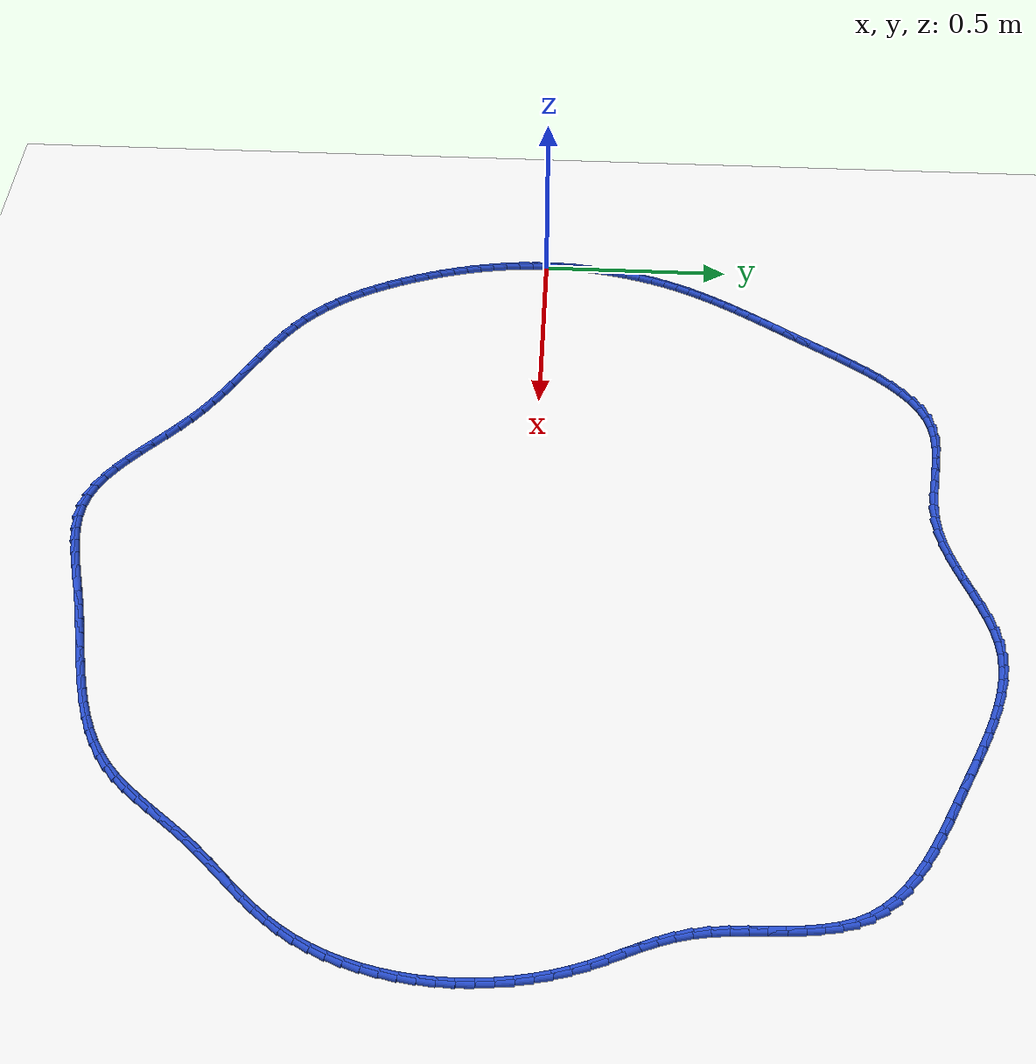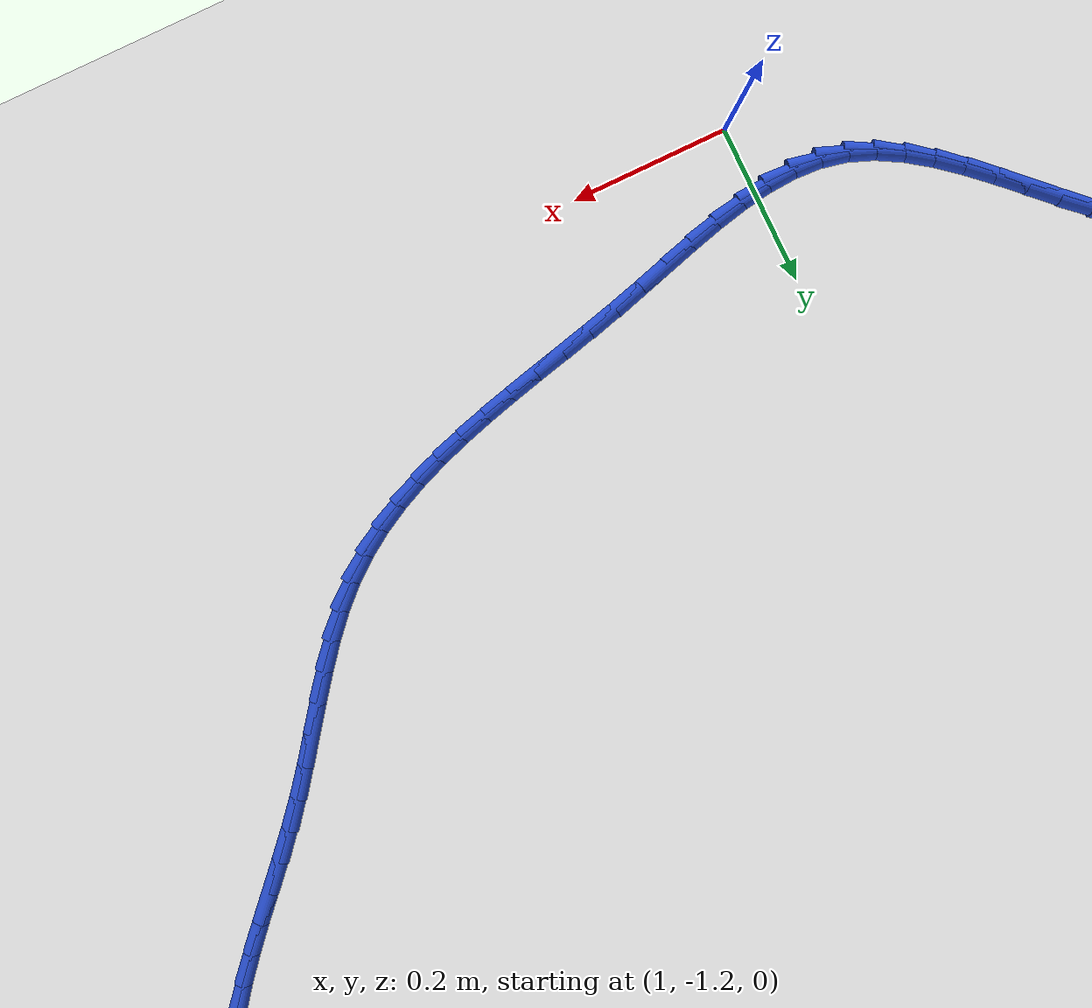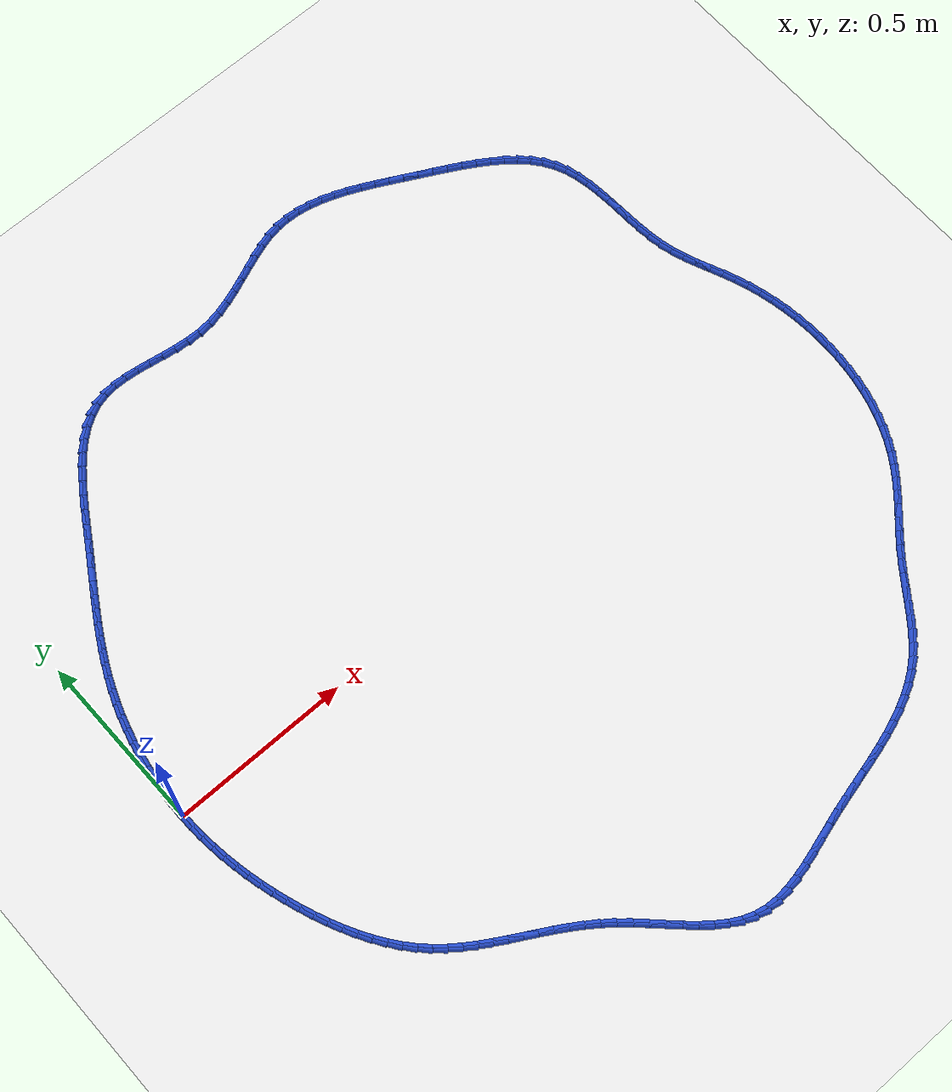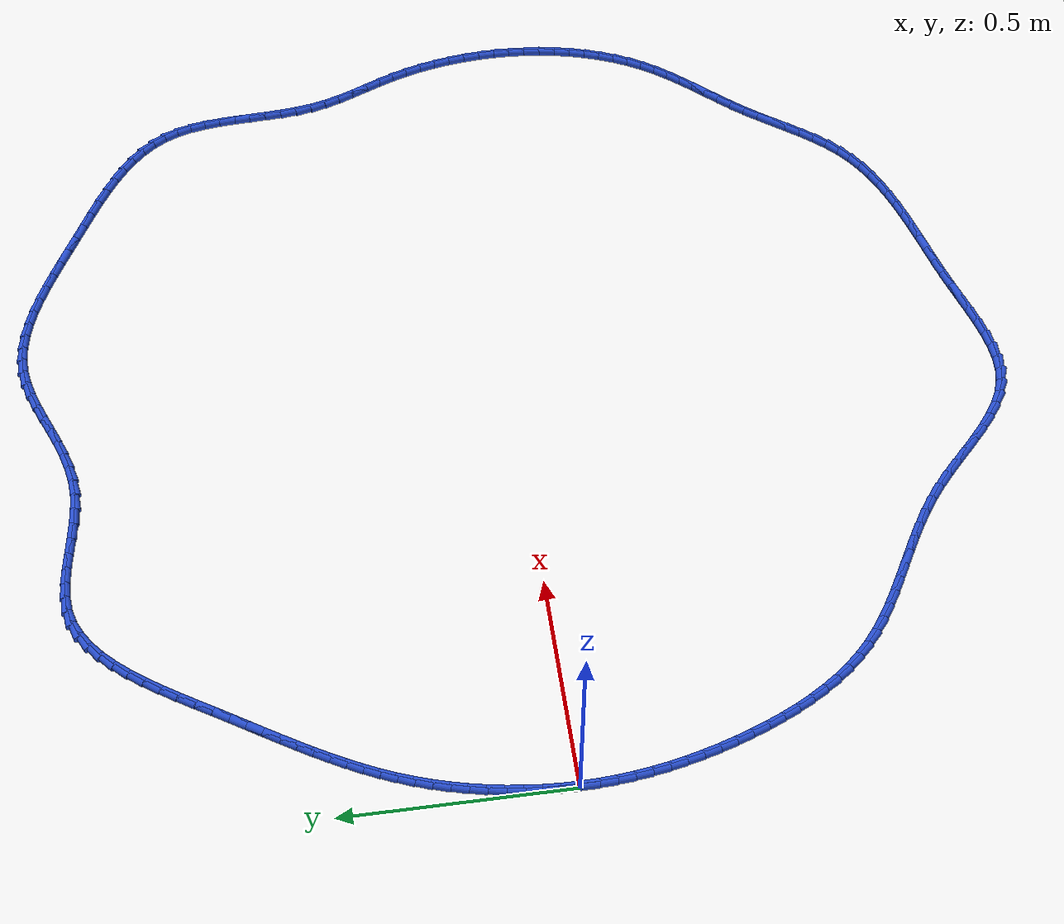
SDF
<sdf version="1.6">
 <world name="default">
  <light name="sun" type="directional">
   <pose>0 0 10 0 -0 0</pose>
   <diffuse>0.8 0.8 0.8 1</diffuse>
   <specular>0.2 0.2 0.2 1</specular>
   <attenuation>
    <range>1000</range>
    <constant>0.9</constant>
    <linear>0.01</linear>
    <quadratic>0.001</quadratic>
   </attenuation>
   <direction>-0.5 0.1 -0.9</direction>
  </light>
  <model name="ground_plane">
   <static>1</static>
   <link name="link">
    <collision name="collision">
     <geometry><plane><normal>0 0 1</normal><size>100 100</size></plane></geometry>
     <surface><friction><ode><mu>100</mu><mu2>50</mu2></ode></friction></surface>
    </collision>
    <visual name="visual">
     <cast_shadows>0</cast_shadows>
     <geometry><plane><normal>0 0 1</normal><size>100 100</size></plane></geometry>
     <material>
      <script><uri>file://media/materials/scripts/gazebo.material</uri><name>Gazebo/WhiteGlow</name></script>
     </material>
    </visual>
   </link>
  </model>
  <gravity>0 0 -9.8</gravity>
  <magnetic_field>6e-06 2.3e-05 -4.2e-05</magnetic_field>
  <atmosphere type="adiabatic"/>
  <physics name="default_physics" default="0" type="ode">
   <max_step_size>0.001</max_step_size>
   <real_time_factor>1</real_time_factor>
   <real_time_update_rate>1000</real_time_update_rate>
  </physics>
  <scene><ambient>0.4 0.4 0.4 1</ambient><background>0.7 0.7 0.7 1</background><shadows>1</shadows></scene>
  <spherical_coordinates>
   <surface_model>EARTH_WGS84</surface_model>
   <latitude_deg>0</latitude_deg>
   <longitude_deg>0</longitude_deg>
   <elevation>0</elevation>
   <heading_deg>0</heading_deg>
  </spherical_coordinates>
  <model name="line">
   <link name="link_0">
    <pose>4.336808689942018e-18 -1.249000902703301e-16 0.01 0 1.57 1.5539545755507613</pose>
    <collision name="collision">
     <geometry><cylinder><radius>0.01</radius><length>0.08</length></cylinder></geometry>
    </collision>
    <visual name="visual">
     <material>
      <script><name>Gazebo/Blue</name><uri>file://media/materials/scripts/gazebo.material</uri></script>
     </material>
     <geometry><cylinder><radius>0.01</radius><length>0.08</length></cylinder></geometry>
    </visual>
   </link>
   <link name="link_1">
    <pose>0.0006335250294052567 0.03761278268761611 0.01 0 1.57 1.515289501972717</pose>
    <collision name="collision">
     <geometry><cylinder><radius>0.01</radius><length>0.08</length></cylinder></geometry>
    </collision>
    <visual name="visual">
     <material>
      <script><name>Gazebo/Blue</name><uri>file://media/materials/scripts/gazebo.material</uri></script>
     </material>
     <geometry><cylinder><radius>0.01</radius><length>0.08</length></cylinder></geometry>
    </visual>
   </link>
   <link name="link_2">
    <pose>0.002727701621116421 0.07530229982100126 0.01 0 1.57 1.4772211700218714</pose>
    <collision name="collision">
     <geometry><cylinder><radius>0.01</radius><length>0.08</length></cylinder></geometry>
    </collision>
    <visual name="visual">
     <material>
      <script><name>Gazebo/Blue</name><uri>file://media/materials/scripts/gazebo.material</uri></script>
     </material>
     <geometry><cylinder><radius>0.01</radius><length>0.08</length></cylinder></geometry>
    </visual>
   </link>
   <link name="link_3">
    <pose>0.006261176008129583 0.11295283746370512 0.01 0 1.57 1.4395035064379358</pose>
    <collision name="collision">
     <geometry><cylinder><radius>0.01</radius><length>0.08</length></cylinder></geometry>
    </collision>
    <visual name="visual">
     <material>
      <script><name>Gazebo/Blue</name><uri>file://media/materials/scripts/gazebo.material</uri></script>
     </material>
     <geometry><cylinder><radius>0.01</radius><length>0.08</length></cylinder></geometry>
    </visual>
   </link>
   <link name="link_4">
    <pose>0.011212594423440836 0.1504486816792772 0.01 0 1.57 1.4018922780809733</pose>
    <collision name="collision">
     <geometry><cylinder><radius>0.01</radius><length>0.08</length></cylinder></geometry>
    </collision>
    <visual name="visual">
     <material>
      <script><name>Gazebo/Blue</name><uri>file://media/materials/scripts/gazebo.material</uri></script>
     </material>
     <geometry><cylinder><radius>0.01</radius><length>0.08</length></cylinder></geometry>
    </visual>
   </link>
   <link name="link_5">
    <pose>0.017560603100046285 0.18767411853126736 0.01 0 1.57 1.3641424240355904</pose>
    <collision name="collision">
     <geometry><cylinder><radius>0.01</radius><length>0.08</length></cylinder></geometry>
    </collision>
    <visual name="visual">
     <material>
      <script><name>Gazebo/Blue</name><uri>file://media/materials/scripts/gazebo.material</uri></script>
     </material>
     <geometry><cylinder><radius>0.01</radius><length>0.08</length></cylinder></geometry>
    </visual>
   </link>
   <link name="link_6">
    <pose>0.02528384827094201 0.22451343408322516 0.01 0 1.57 1.326005252063748</pose>
    <collision name="collision">
     <geometry><cylinder><radius>0.01</radius><length>0.08</length></cylinder></geometry>
    </collision>
    <visual name="visual">
     <material>
      <script><name>Gazebo/Blue</name><uri>file://media/materials/scripts/gazebo.material</uri></script>
     </material>
     <geometry><cylinder><radius>0.01</radius><length>0.08</length></cylinder></geometry>
    </visual>
   </link>
   <link name="link_7">
    <pose>0.03436097616912411 0.2608509143987004 0.01 0 1.57 1.2872255732784494</pose>
    <collision name="collision">
     <geometry><cylinder><radius>0.01</radius><length>0.08</length></cylinder></geometry>
    </collision>
    <visual name="visual">
     <material>
      <script><name>Gazebo/Blue</name><uri>file://media/materials/scripts/gazebo.material</uri></script>
     </material>
     <geometry><cylinder><radius>0.01</radius><length>0.08</length></cylinder></geometry>
    </visual>
   </link>
   <link name="link_8">
    <pose>0.044770633027588685 0.2965708455412427 0.01 0 1.57 1.2475388583686626</pose>
    <collision name="collision">
     <geometry><cylinder><radius>0.01</radius><length>0.08</length></cylinder></geometry>
    </collision>
    <visual name="visual">
     <material>
      <script><name>Gazebo/Blue</name><uri>file://media/materials/scripts/gazebo.material</uri></script>
     </material>
     <geometry><cylinder><radius>0.01</radius><length>0.08</length></cylinder></geometry>
    </visual>
   </link>
   <link name="link_9">
    <pose>0.056491465079331823 0.3315575135744017 0.01 0 1.57 1.206916690669785</pose>
    <collision name="collision">
     <geometry><cylinder><radius>0.01</radius><length>0.08</length></cylinder></geometry>
    </collision>
    <visual name="visual">
     <material>
      <script><name>Gazebo/Blue</name><uri>file://media/materials/scripts/gazebo.material</uri></script>
     </material>
     <geometry><cylinder><radius>0.01</radius><length>0.08</length></cylinder></geometry>
    </visual>
   </link>
   <link name="link_10">
    <pose>0.06949816466066101 0.36571029598296767 0.01 0 1.57 1.1678840294439143</pose>
    <collision name="collision">
     <geometry><cylinder><radius>0.01</radius><length>0.08</length></cylinder></geometry>
    </collision>
    <visual name="visual">
     <material>
      <script><name>Gazebo/Blue</name><uri>file://media/materials/scripts/gazebo.material</uri></script>
     </material>
     <geometry><cylinder><radius>0.01</radius><length>0.08</length></cylinder></geometry>
    </visual>
   </link>
   <link name="link_11">
    <pose>0.08372407315496913 0.39908640053873257 0.01 0 1.57 1.1324112349614608</pose>
    <collision name="collision">
     <geometry><cylinder><radius>0.01</radius><length>0.08</length></cylinder></geometry>
    </collision>
    <visual name="visual">
     <material>
      <script><name>Gazebo/Blue</name><uri>file://media/materials/scripts/gazebo.material</uri></script>
     </material>
     <geometry><cylinder><radius>0.01</radius><length>0.08</length></cylinder></geometry>
    </visual>
   </link>
   <link name="link_12">
    <pose>0.09907789264635085 0.43183707946484 0.01 0 1.57 1.1009415273770418</pose>
    <collision name="collision">
     <geometry><cylinder><radius>0.01</radius><length>0.08</length></cylinder></geometry>
    </collision>
    <visual name="visual">
     <material>
      <script><name>Gazebo/Blue</name><uri>file://media/materials/scripts/gazebo.material</uri></script>
     </material>
     <geometry><cylinder><radius>0.01</radius><length>0.08</length></cylinder></geometry>
    </visual>
   </link>
   <link name="link_13">
    <pose>0.11546799715522622 0.4641148371534965 0.01 0 1.57 1.0737801264386635</pose>
    <collision name="collision">
     <geometry><cylinder><radius>0.01</radius><length>0.08</length></cylinder></geometry>
    </collision>
    <visual name="visual">
     <material>
      <script><name>Gazebo/Blue</name><uri>file://media/materials/scripts/gazebo.material</uri></script>
     </material>
     <geometry><cylinder><radius>0.01</radius><length>0.08</length></cylinder></geometry>
    </visual>
   </link>
   <link name="link_14">
    <pose>0.1328027607020151 0.49607217799690784 0.01 0 1.57 1.0511189738767226</pose>
    <collision name="collision">
     <geometry><cylinder><radius>0.01</radius><length>0.08</length></cylinder></geometry>
    </collision>
    <visual name="visual">
     <material>
      <script><name>Gazebo/Blue</name><uri>file://media/materials/scripts/gazebo.material</uri></script>
     </material>
     <geometry><cylinder><radius>0.01</radius><length>0.08</length></cylinder></geometry>
    </visual>
   </link>
   <link name="link_15">
    <pose>0.15099055730713767 0.5278616063872809 0.01 0 1.57 1.0330471737703797</pose>
    <collision name="collision">
     <geometry><cylinder><radius>0.01</radius><length>0.08</length></cylinder></geometry>
    </collision>
    <visual name="visual">
     <material>
      <script><name>Gazebo/Blue</name><uri>file://media/materials/scripts/gazebo.material</uri></script>
     </material>
     <geometry><cylinder><radius>0.01</radius><length>0.08</length></cylinder></geometry>
    </visual>
   </link>
   <link name="link_16">
    <pose>0.16993976099101357 0.5596356267168211 0.01 0 1.57 1.0195648011040894</pose>
    <collision name="collision">
     <geometry><cylinder><radius>0.01</radius><length>0.08</length></cylinder></geometry>
    </collision>
    <visual name="visual">
     <material>
      <script><name>Gazebo/Blue</name><uri>file://media/materials/scripts/gazebo.material</uri></script>
     </material>
     <geometry><cylinder><radius>0.01</radius><length>0.08</length></cylinder></geometry>
    </visual>
   </link>
   <link name="link_17">
    <pose>0.18955874577406304 0.5915467433777352 0.01 0 1.57 1.0105976096031455</pose>
    <collision name="collision">
     <geometry><cylinder><radius>0.01</radius><length>0.08</length></cylinder></geometry>
    </collision>
    <visual name="visual">
     <material>
      <script><name>Gazebo/Blue</name><uri>file://media/materials/scripts/gazebo.material</uri></script>
     </material>
     <geometry><cylinder><radius>0.01</radius><length>0.08</length></cylinder></geometry>
    </visual>
   </link>
   <link name="link_18">
    <pose>0.20975588567670603 0.6237474607622294 0.01 0 1.57 1.0060109094418814</pose>
    <collision name="collision">
     <geometry><cylinder><radius>0.01</radius><length>0.08</length></cylinder></geometry>
    </collision>
    <visual name="visual">
     <material>
      <script><name>Gazebo/Blue</name><uri>file://media/materials/scripts/gazebo.material</uri></script>
     </material>
     <geometry><cylinder><radius>0.01</radius><length>0.08</length></cylinder></geometry>
    </visual>
   </link>
   <link name="link_19">
    <pose>0.23043955471936228 0.6563902832625095 0.01 0 1.57 1.0056216467435408</pose>
    <collision name="collision">
     <geometry><cylinder><radius>0.01</radius><length>0.08</length></cylinder></geometry>
    </collision>
    <visual name="visual">
     <material>
      <script><name>Gazebo/Blue</name><uri>file://media/materials/scripts/gazebo.material</uri></script>
     </material>
     <geometry><cylinder><radius>0.01</radius><length>0.08</length></cylinder></geometry>
    </visual>
   </link>
   <link name="link_20">
    <pose>0.25151812692245207 0.6896277152707824 0.01 0 1.57 1.0092076376877115</pose>
    <collision name="collision">
     <geometry><cylinder><radius>0.01</radius><length>0.08</length></cylinder></geometry>
    </collision>
    <visual name="visual">
     <material>
      <script><name>Gazebo/Blue</name><uri>file://media/materials/scripts/gazebo.material</uri></script>
     </material>
     <geometry><cylinder><radius>0.01</radius><length>0.08</length></cylinder></geometry>
    </visual>
   </link>
   <link name="link_21">
    <pose>0.2728999876396685 0.7236122255249691 0.01 0 1.57 1.013492906386332</pose>
    <collision name="collision">
     <geometry><cylinder><radius>0.01</radius><length>0.08</length></cylinder></geometry>
    </collision>
    <visual name="visual">
     <material>
      <script><name>Gazebo/Blue</name><uri>file://media/materials/scripts/gazebo.material</uri></script>
     </material>
     <geometry><cylinder><radius>0.01</radius><length>0.08</length></cylinder></geometry>
    </visual>
   </link>
   <link name="link_22">
    <pose>0.2945429002526329 0.7583409403275332 0.01 0 1.57 1.0086024646270246</pose>
    <collision name="collision">
     <geometry><cylinder><radius>0.01</radius><length>0.08</length></cylinder></geometry>
    </collision>
    <visual name="visual">
     <material>
      <script><name>Gazebo/Blue</name><uri>file://media/materials/scripts/gazebo.material</uri></script>
     </material>
     <geometry><cylinder><radius>0.01</radius><length>0.08</length></cylinder></geometry>
    </visual>
   </link>
   <link name="link_23">
    <pose>0.31656718799494277 0.7932995754533597 0.01 0 1.57 0.9926048124117438</pose>
    <collision name="collision">
     <geometry><cylinder><radius>0.01</radius><length>0.08</length></cylinder></geometry>
    </collision>
    <visual name="visual">
     <material>
      <script><name>Gazebo/Blue</name><uri>file://media/materials/scripts/gazebo.material</uri></script>
     </material>
     <geometry><cylinder><radius>0.01</radius><length>0.08</length></cylinder></geometry>
    </visual>
   </link>
   <link name="link_24">
    <pose>0.3391265781076931 0.8278687582382754 0.01 0 1.57 0.9649671843474599</pose>
    <collision name="collision">
     <geometry><cylinder><radius>0.01</radius><length>0.08</length></cylinder></geometry>
    </collision>
    <visual name="visual">
     <material>
      <script><name>Gazebo/Blue</name><uri>file://media/materials/scripts/gazebo.material</uri></script>
     </material>
     <geometry><cylinder><radius>0.01</radius><length>0.08</length></cylinder></geometry>
    </visual>
   </link>
   <link name="link_25">
    <pose>0.36237479783197885 0.8614291160181077 0.01 0 1.57 0.9244621094450041</pose>
    <collision name="collision">
     <geometry><cylinder><radius>0.01</radius><length>0.08</length></cylinder></geometry>
    </collision>
    <visual name="visual">
     <material>
      <script><name>Gazebo/Blue</name><uri>file://media/materials/scripts/gazebo.material</uri></script>
     </material>
     <geometry><cylinder><radius>0.01</radius><length>0.08</length></cylinder></geometry>
    </visual>
   </link>
   <link name="link_26">
    <pose>0.3864655744088949 0.8933612761286835 0.01 0 1.57 0.8691417891271033</pose>
    <collision name="collision">
     <geometry><cylinder><radius>0.01</radius><length>0.08</length></cylinder></geometry>
    </collision>
    <visual name="visual">
     <material>
      <script><name>Gazebo/Blue</name><uri>file://media/materials/scripts/gazebo.material</uri></script>
     </material>
     <geometry><cylinder><radius>0.01</radius><length>0.08</length></cylinder></geometry>
    </visual>
   </link>
   <link name="link_27">
    <pose>0.4115526350795362 0.9230458659058305 0.01 0 1.57 0.7963406698289079</pose>
    <collision name="collision">
     <geometry><cylinder><radius>0.01</radius><length>0.08</length></cylinder></geometry>
    </collision>
    <visual name="visual">
     <material>
      <script><name>Gazebo/Blue</name><uri>file://media/materials/scripts/gazebo.material</uri></script>
     </material>
     <geometry><cylinder><radius>0.01</radius><length>0.08</length></cylinder></geometry>
    </visual>
   </link>
   <link name="link_28">
    <pose>0.43778970708499776 0.9498635126853752 0.01 0 1.57 0.7028399843261701</pose>
    <collision name="collision">
     <geometry><cylinder><radius>0.01</radius><length>0.08</length></cylinder></geometry>
    </collision>
    <visual name="visual">
     <material>
      <script><name>Gazebo/Blue</name><uri>file://media/materials/scripts/gazebo.material</uri></script>
     </material>
     <geometry><cylinder><radius>0.01</radius><length>0.08</length></cylinder></geometry>
    </visual>
   </link>
   <link name="link_29">
    <pose>0.4653305176663744 0.973194843803145 0.01 0 1.57 0.5854547069448987</pose>
    <collision name="collision">
     <geometry><cylinder><radius>0.01</radius><length>0.08</length></cylinder></geometry>
    </collision>
    <visual name="visual">
     <material>
      <script><name>Gazebo/Blue</name><uri>file://media/materials/scripts/gazebo.material</uri></script>
     </material>
     <geometry><cylinder><radius>0.01</radius><length>0.08</length></cylinder></geometry>
    </visual>
   </link>
   <link name="link_30">
    <pose>0.49432879406476116 0.9924204865949673 0.01 0 1.57 0.442410495497921</pose>
    <collision name="collision">
     <geometry><cylinder><radius>0.01</radius><length>0.08</length></cylinder></geometry>
    </collision>
    <visual name="visual">
     <material>
      <script><name>Gazebo/Blue</name><uri>file://media/materials/scripts/gazebo.material</uri></script>
     </material>
     <geometry><cylinder><radius>0.01</radius><length>0.08</length></cylinder></geometry>
    </visual>
   </link>
   <link name="link_31">
    <pose>0.5249382635212527 1.006921068396669 0.01 0 1.57 0.2758011422567</pose>
    <collision name="collision">
     <geometry><cylinder><radius>0.01</radius><length>0.08</length></cylinder></geometry>
    </collision>
    <visual name="visual">
     <material>
      <script><name>Gazebo/Blue</name><uri>file://media/materials/scripts/gazebo.material</uri></script>
     </material>
     <geometry><cylinder><radius>0.01</radius><length>0.08</length></cylinder></geometry>
    </visual>
   </link>
   <link name="link_32">
    <pose>0.5573112078425622 1.0160830561401628 0.01 0 1.57 0.11091420878421225</pose>
    <collision name="collision">
     <geometry><cylinder><radius>0.01</radius><length>0.08</length></cylinder></geometry>
    </collision>
    <visual name="visual">
     <material>
      <script><name>Gazebo/Blue</name><uri>file://media/materials/scripts/gazebo.material</uri></script>
     </material>
     <geometry><cylinder><radius>0.01</radius><length>0.08</length></cylinder></geometry>
    </visual>
   </link>
   <link name="link_33">
    <pose>0.5914532315949727 1.0198854969877424 0.01 0 1.57 -0.013574645325719763</pose>
    <collision name="collision">
     <geometry><cylinder><radius>0.01</radius><length>0.08</length></cylinder></geometry>
    </collision>
    <visual name="visual">
     <material>
      <script><name>Gazebo/Blue</name><uri>file://media/materials/scripts/gazebo.material</uri></script>
     </material>
     <geometry><cylinder><radius>0.01</radius><length>0.08</length></cylinder></geometry>
    </visual>
   </link>
   <link name="link_34">
    <pose>0.6270991123007051 1.0194015870759536 0.01 0 1.57 -0.09680402853373943</pose>
    <collision name="collision">
     <geometry><cylinder><radius>0.01</radius><length>0.08</length></cylinder></geometry>
    </collision>
    <visual name="visual">
     <material>
      <script><name>Gazebo/Blue</name><uri>file://media/materials/scripts/gazebo.material</uri></script>
     </material>
     <geometry><cylinder><radius>0.01</radius><length>0.08</length></cylinder></geometry>
    </visual>
   </link>
   <link name="link_35">
    <pose>0.6639543852991328 1.015822661793205 0.01 0 1.57 -0.1441500881530438</pose>
    <collision name="collision">
     <geometry><cylinder><radius>0.01</radius><length>0.08</length></cylinder></geometry>
    </collision>
    <visual name="visual">
     <material>
      <script><name>Gazebo/Blue</name><uri>file://media/materials/scripts/gazebo.material</uri></script>
     </material>
     <geometry><cylinder><radius>0.01</radius><length>0.08</length></cylinder></geometry>
    </visual>
   </link>
   <link name="link_36">
    <pose>0.7017245859296278 1.0103400565279046 0.01 0 1.57 -0.1599869326057495</pose>
    <collision name="collision">
     <geometry><cylinder><radius>0.01</radius><length>0.08</length></cylinder></geometry>
    </collision>
    <visual name="visual">
     <material>
      <script><name>Gazebo/Blue</name><uri>file://media/materials/scripts/gazebo.material</uri></script>
     </material>
     <geometry><cylinder><radius>0.01</radius><length>0.08</length></cylinder></geometry>
    </visual>
   </link>
   <link name="link_37">
    <pose>0.7401152495315626 1.0041451066684606 0.01 0 1.57 -0.1465768145054736</pose>
    <collision name="collision">
     <geometry><cylinder><radius>0.01</radius><length>0.08</length></cylinder></geometry>
    </collision>
    <visual name="visual">
     <material>
      <script><name>Gazebo/Blue</name><uri>file://media/materials/scripts/gazebo.material</uri></script>
     </material>
     <geometry><cylinder><radius>0.01</radius><length>0.08</length></cylinder></geometry>
    </visual>
   </link>
   <link name="link_38">
    <pose>0.7788319114443096 0.998429147603281 0.01 0 1.57 -0.10403136529894218</pose>
    <collision name="collision">
     <geometry><cylinder><radius>0.01</radius><length>0.08</length></cylinder></geometry>
    </collision>
    <visual name="visual">
     <material>
      <script><name>Gazebo/Blue</name><uri>file://media/materials/scripts/gazebo.material</uri></script>
     </material>
     <geometry><cylinder><radius>0.01</radius><length>0.08</length></cylinder></geometry>
    </visual>
   </link>
   <link name="link_39">
    <pose>0.817580107007242 0.9943835147207748 0.01 0 1.57 -0.030754576267320255</pose>
    <collision name="collision">
     <geometry><cylinder><radius>0.01</radius><length>0.08</length></cylinder></geometry>
    </collision>
    <visual name="visual">
     <material>
      <script><name>Gazebo/Blue</name><uri>file://media/materials/scripts/gazebo.material</uri></script>
     </material>
     <geometry><cylinder><radius>0.01</radius><length>0.08</length></cylinder></geometry>
    </visual>
   </link>
   <link name="link_40">
    <pose>0.8560653715597314 0.9931995434093488 0.01 0 1.57 0.0746664247674037</pose>
    <collision name="collision">
     <geometry><cylinder><radius>0.01</radius><length>0.08</length></cylinder></geometry>
    </collision>
    <visual name="visual">
     <material>
      <script><name>Gazebo/Blue</name><uri>file://media/materials/scripts/gazebo.material</uri></script>
     </material>
     <geometry><cylinder><radius>0.01</radius><length>0.08</length></cylinder></geometry>
    </visual>
   </link>
   <link name="link_41">
    <pose>0.8939987156026123 0.9960371658688199 0.01 0 1.57 0.1873155831965177</pose>
    <collision name="collision">
     <geometry><cylinder><radius>0.01</radius><length>0.08</length></cylinder></geometry>
    </collision>
    <visual name="visual">
     <material>
      <script><name>Gazebo/Blue</name><uri>file://media/materials/scripts/gazebo.material</uri></script>
     </material>
     <geometry><cylinder><radius>0.01</radius><length>0.08</length></cylinder></geometry>
    </visual>
   </link>
   <link name="link_42">
    <pose>0.9312580222862883 1.003099204025243 0.01 0 1.57 0.2759463623427365</pose>
    <collision name="collision">
     <geometry><cylinder><radius>0.01</radius><length>0.08</length></cylinder></geometry>
    </collision>
    <visual name="visual">
     <material>
      <script><name>Gazebo/Blue</name><uri>file://media/materials/scripts/gazebo.material</uri></script>
     </material>
     <geometry><cylinder><radius>0.01</radius><length>0.08</length></cylinder></geometry>
    </visual>
   </link>
   <link name="link_43">
    <pose>0.9679145678495793 1.0134792596162487 0.01 0 1.57 0.3386970586274794</pose>
    <collision name="collision">
     <geometry><cylinder><radius>0.01</radius><length>0.08</length></cylinder></geometry>
    </collision>
    <visual name="visual">
     <material>
      <script><name>Gazebo/Blue</name><uri>file://media/materials/scripts/gazebo.material</uri></script>
     </material>
     <geometry><cylinder><radius>0.01</radius><length>0.08</length></cylinder></geometry>
    </visual>
   </link>
   <link name="link_44">
    <pose>1.0040504439782332 1.026208901593413 0.01 0 1.57 0.3764397459259317</pose>
    <collision name="collision">
     <geometry><cylinder><radius>0.01</radius><length>0.08</length></cylinder></geometry>
    </collision>
    <visual name="visual">
     <material>
      <script><name>Gazebo/Blue</name><uri>file://media/materials/scripts/gazebo.material</uri></script>
     </material>
     <geometry><cylinder><radius>0.01</radius><length>0.08</length></cylinder></geometry>
    </visual>
   </link>
   <link name="link_45">
    <pose>1.0397477423579957 1.0403196989083119 0.01 0 1.57 0.3899154456964672</pose>
    <collision name="collision">
     <geometry><cylinder><radius>0.01</radius><length>0.08</length></cylinder></geometry>
    </collision>
    <visual name="visual">
     <material>
      <script><name>Gazebo/Blue</name><uri>file://media/materials/scripts/gazebo.material</uri></script>
     </material>
     <geometry><cylinder><radius>0.01</radius><length>0.08</length></cylinder></geometry>
    </visual>
   </link>
   <link name="link_46">
    <pose>1.0750885546746156 1.0548432205125227 0.01 0 1.57 0.3790611823252952</pose>
    <collision name="collision">
     <geometry><cylinder><radius>0.01</radius><length>0.08</length></cylinder></geometry>
    </collision>
    <visual name="visual">
     <material>
      <script><name>Gazebo/Blue</name><uri>file://media/materials/scripts/gazebo.material</uri></script>
     </material>
     <geometry><cylinder><radius>0.01</radius><length>0.08</length></cylinder></geometry>
    </visual>
   </link>
   <link name="link_47">
    <pose>1.1101549726138393 1.0688110353576217 0.01 0 1.57 0.3427349114920555</pose>
    <collision name="collision">
     <geometry><cylinder><radius>0.01</radius><length>0.08</length></cylinder></geometry>
    </collision>
    <visual name="visual">
     <material>
      <script><name>Gazebo/Blue</name><uri>file://media/materials/scripts/gazebo.material</uri></script>
     </material>
     <geometry><cylinder><radius>0.01</radius><length>0.08</length></cylinder></geometry>
    </visual>
   </link>
   <link name="link_48">
    <pose>1.1450290878614144 1.081254712395185 0.01 0 1.57 0.27879329243875894</pose>
    <collision name="collision">
     <geometry><cylinder><radius>0.01</radius><length>0.08</length></cylinder></geometry>
    </collision>
    <visual name="visual">
     <material>
      <script><name>Gazebo/Blue</name><uri>file://media/materials/scripts/gazebo.material</uri></script>
     </material>
     <geometry><cylinder><radius>0.01</radius><length>0.08</length></cylinder></geometry>
    </visual>
   </link>
   <link name="link_49">
    <pose>1.179792992103088 1.091205820576789 0.01 0 1.57 0.1847123536411379</pose>
    <collision name="collision">
     <geometry><cylinder><radius>0.01</radius><length>0.08</length></cylinder></geometry>
    </collision>
    <visual name="visual">
     <material>
      <script><name>Gazebo/Blue</name><uri>file://media/materials/scripts/gazebo.material</uri></script>
     </material>
     <geometry><cylinder><radius>0.01</radius><length>0.08</length></cylinder></geometry>
    </visual>
   </link>
   <link name="link_50">
    <pose>1.2145287770246074 1.09769592885401 0.01 0 1.57 0.06416200103219727</pose>
    <collision name="collision">
     <geometry><cylinder><radius>0.01</radius><length>0.08</length></cylinder></geometry>
    </collision>
    <visual name="visual">
     <material>
      <script><name>Gazebo/Blue</name><uri>file://media/materials/scripts/gazebo.material</uri></script>
     </material>
     <geometry><cylinder><radius>0.01</radius><length>0.08</length></cylinder></geometry>
    </visual>
   </link>
   <link name="link_51">
    <pose>1.249310390346295 1.0999306542169203 0.01 0 1.57 -0.0541422027024987</pose>
    <collision name="collision">
     <geometry><cylinder><radius>0.01</radius><length>0.08</length></cylinder></geometry>
    </collision>
    <visual name="visual">
     <material>
      <script><name>Gazebo/Blue</name><uri>file://media/materials/scripts/gazebo.material</uri></script>
     </material>
     <geometry><cylinder><radius>0.01</radius><length>0.08</length></cylinder></geometry>
    </visual>
   </link>
   <link name="link_52">
    <pose>1.2841684554701638 1.0980415155016978 0.01 0 1.57 -0.15817192943619007</pose>
    <collision name="collision">
     <geometry><cylinder><radius>0.01</radius><length>0.08</length></cylinder></geometry>
    </collision>
    <visual name="visual">
     <material>
      <script><name>Gazebo/Blue</name><uri>file://media/materials/scripts/gazebo.material</uri></script>
     </material>
     <geometry><cylinder><radius>0.01</radius><length>0.08</length></cylinder></geometry>
    </visual>
   </link>
   <link name="link_53">
    <pose>1.3191192457168404 1.0924667130426873 0.01 0 1.57 -0.2465115295069356</pose>
    <collision name="collision">
     <geometry><cylinder><radius>0.01</radius><length>0.08</length></cylinder></geometry>
    </collision>
    <visual name="visual">
     <material>
      <script><name>Gazebo/Blue</name><uri>file://media/materials/scripts/gazebo.material</uri></script>
     </material>
     <geometry><cylinder><radius>0.01</radius><length>0.08</length></cylinder></geometry>
    </visual>
   </link>
   <link name="link_54">
    <pose>1.3541790251305217 1.0836446454246573 0.01 0 1.57 -0.31925683191862525</pose>
    <collision name="collision">
     <geometry><cylinder><radius>0.01</radius><length>0.08</length></cylinder></geometry>
    </collision>
    <visual name="visual">
     <material>
      <script><name>Gazebo/Blue</name><uri>file://media/materials/scripts/gazebo.material</uri></script>
     </material>
     <geometry><cylinder><radius>0.01</radius><length>0.08</length></cylinder></geometry>
    </visual>
   </link>
   <link name="link_55">
    <pose>1.3893640577554038 1.0720137112323747 0.01 0 1.57 -0.37734912172325175</pose>
    <collision name="collision">
     <geometry><cylinder><radius>0.01</radius><length>0.08</length></cylinder></geometry>
    </collision>
    <visual name="visual">
     <material>
      <script><name>Gazebo/Blue</name><uri>file://media/materials/scripts/gazebo.material</uri></script>
     </material>
     <geometry><cylinder><radius>0.01</radius><length>0.08</length></cylinder></geometry>
    </visual>
   </link>
   <link name="link_56">
    <pose>1.4246906076356827 1.058012309050608 0.01 0 1.57 -0.4220456286937595</pose>
    <collision name="collision">
     <geometry><cylinder><radius>0.01</radius><length>0.08</length></cylinder></geometry>
    </collision>
    <visual name="visual">
     <material>
      <script><name>Gazebo/Blue</name><uri>file://media/materials/scripts/gazebo.material</uri></script>
     </material>
     <geometry><cylinder><radius>0.01</radius><length>0.08</length></cylinder></geometry>
    </visual>
   </link>
   <link name="link_57">
    <pose>1.4601749388155547 1.042078837464124 0.01 0 1.57 -0.4545870454215999</pose>
    <collision name="collision">
     <geometry><cylinder><radius>0.01</radius><length>0.08</length></cylinder></geometry>
    </collision>
    <visual name="visual">
     <material>
      <script><name>Gazebo/Blue</name><uri>file://media/materials/scripts/gazebo.material</uri></script>
     </material>
     <geometry><cylinder><radius>0.01</radius><length>0.08</length></cylinder></geometry>
    </visual>
   </link>
   <link name="link_58">
    <pose>1.4958333153392176 1.0246516950576912 0.01 0 1.57 -0.4760238457133835</pose>
    <collision name="collision">
     <geometry><cylinder><radius>0.01</radius><length>0.08</length></cylinder></geometry>
    </collision>
    <visual name="visual">
     <material>
      <script><name>Gazebo/Blue</name><uri>file://media/materials/scripts/gazebo.material</uri></script>
     </material>
     <geometry><cylinder><radius>0.01</radius><length>0.08</length></cylinder></geometry>
    </visual>
   </link>
   <link name="link_59">
    <pose>1.5316820012508652 1.006169280416077 0.01 0 1.57 -0.4871420438049215</pose>
    <collision name="collision">
     <geometry><cylinder><radius>0.01</radius><length>0.08</length></cylinder></geometry>
    </collision>
    <visual name="visual">
     <material>
      <script><name>Gazebo/Blue</name><uri>file://media/materials/scripts/gazebo.material</uri></script>
     </material>
     <geometry><cylinder><radius>0.01</radius><length>0.08</length></cylinder></geometry>
    </visual>
   </link>
   <link name="link_60">
    <pose>1.5677372605946958 0.9870699921240488 0.01 0 1.57 -0.4884539452697681</pose>
    <collision name="collision">
     <geometry><cylinder><radius>0.01</radius><length>0.08</length></cylinder></geometry>
    </collision>
    <visual name="visual">
     <material>
      <script><name>Gazebo/Blue</name><uri>file://media/materials/scripts/gazebo.material</uri></script>
     </material>
     <geometry><cylinder><radius>0.01</radius><length>0.08</length></cylinder></geometry>
    </visual>
   </link>
   <link name="link_61">
    <pose>1.6040150842442444 0.9677918162568404 0.01 0 1.57 -0.4852311230544129</pose>
    <collision name="collision">
     <geometry><cylinder><radius>0.01</radius><length>0.08</length></cylinder></geometry>
    </collision>
    <visual name="visual">
     <material>
      <script><name>Gazebo/Blue</name><uri>file://media/materials/scripts/gazebo.material</uri></script>
     </material>
     <geometry><cylinder><radius>0.01</radius><length>0.08</length></cylinder></geometry>
    </visual>
   </link>
   <link name="link_62">
    <pose>1.6404160164709705 0.9485984052916058 0.01 0 1.57 -0.49037742284695524</pose>
    <collision name="collision">
     <geometry><cylinder><radius>0.01</radius><length>0.08</length></cylinder></geometry>
    </collision>
    <visual name="visual">
     <material>
      <script><name>Gazebo/Blue</name><uri>file://media/materials/scripts/gazebo.material</uri></script>
     </material>
     <geometry><cylinder><radius>0.01</radius><length>0.08</length></cylinder></geometry>
    </visual>
   </link>
   <link name="link_63">
    <pose>1.6765465093799068 0.9293093090241081 0.01 0 1.57 -0.5061690376673833</pose>
    <collision name="collision">
     <geometry><cylinder><radius>0.01</radius><length>0.08</length></cylinder></geometry>
    </collision>
    <visual name="visual">
     <material>
      <script><name>Gazebo/Blue</name><uri>file://media/materials/scripts/gazebo.material</uri></script>
     </material>
     <geometry><cylinder><radius>0.01</radius><length>0.08</length></cylinder></geometry>
    </visual>
   </link>
   <link name="link_64">
    <pose>1.7119668687185632 0.9096743925612568 0.01 0 1.57 -0.533277753319224</pose>
    <collision name="collision">
     <geometry><cylinder><radius>0.01</radius><length>0.08</length></cylinder></geometry>
    </collision>
    <visual name="visual">
     <material>
      <script><name>Gazebo/Blue</name><uri>file://media/materials/scripts/gazebo.material</uri></script>
     </material>
     <geometry><cylinder><radius>0.01</radius><length>0.08</length></cylinder></geometry>
    </visual>
   </link>
   <link name="link_65">
    <pose>1.7462374002344507 0.8894435210099612 0.01 0 1.57 -0.5728027711901966</pose>
    <collision name="collision">
     <geometry><cylinder><radius>0.01</radius><length>0.08</length></cylinder></geometry>
    </collision>
    <visual name="visual">
     <material>
      <script><name>Gazebo/Blue</name><uri>file://media/materials/scripts/gazebo.material</uri></script>
     </material>
     <geometry><cylinder><radius>0.01</radius><length>0.08</length></cylinder></geometry>
    </visual>
   </link>
   <link name="link_66">
    <pose>1.778918409675081 0.8683665594771303 0.01 0 1.57 -0.626251775047361</pose>
    <collision name="collision">
     <geometry><cylinder><radius>0.01</radius><length>0.08</length></cylinder></geometry>
    </collision>
    <visual name="visual">
     <material>
      <script><name>Gazebo/Blue</name><uri>file://media/materials/scripts/gazebo.material</uri></script>
     </material>
     <geometry><cylinder><radius>0.01</radius><length>0.08</length></cylinder></geometry>
    </visual>
   </link>
   <link name="link_67">
    <pose>1.8095702027879634 0.8461933730696737 0.01 0 1.57 -0.6954458725464926</pose>
    <collision name="collision">
     <geometry><cylinder><radius>0.01</radius><length>0.08</length></cylinder></geometry>
    </collision>
    <visual name="visual">
     <material>
      <script><name>Gazebo/Blue</name><uri>file://media/materials/scripts/gazebo.material</uri></script>
     </material>
     <geometry><cylinder><radius>0.01</radius><length>0.08</length></cylinder></geometry>
    </visual>
   </link>
   <link name="link_68">
    <pose>1.8377530853206092 0.8226738268945007 0.01 0 1.57 -0.7822579501895124</pose>
    <collision name="collision">
     <geometry><cylinder><radius>0.01</radius><length>0.08</length></cylinder></geometry>
    </collision>
    <visual name="visual">
     <material>
      <script><name>Gazebo/Blue</name><uri>file://media/materials/scripts/gazebo.material</uri></script>
     </material>
     <geometry><cylinder><radius>0.01</radius><length>0.08</length></cylinder></geometry>
    </visual>
   </link>
   <link name="link_69">
    <pose>1.8630273630205296 0.7975577860585206 0.01 0 1.57 -0.8880597192138523</pose>
    <collision name="collision">
     <geometry><cylinder><radius>0.01</radius><length>0.08</length></cylinder></geometry>
    </collision>
    <visual name="visual">
     <material>
      <script><name>Gazebo/Blue</name><uri>file://media/materials/scripts/gazebo.material</uri></script>
     </material>
     <geometry><cylinder><radius>0.01</radius><length>0.08</length></cylinder></geometry>
    </visual>
   </link>
   <link name="link_70">
    <pose>1.8849533416352353 0.7705951156686427 0.01 0 1.57 -1.0127951322347941</pose>
    <collision name="collision">
     <geometry><cylinder><radius>0.01</radius><length>0.08</length></cylinder></geometry>
    </collision>
    <visual name="visual">
     <material>
      <script><name>Gazebo/Blue</name><uri>file://media/materials/scripts/gazebo.material</uri></script>
     </material>
     <geometry><cylinder><radius>0.01</radius><length>0.08</length></cylinder></geometry>
    </visual>
   </link>
   <link name="link_71">
    <pose>1.9030913269122365 0.7415356808317761 0.01 0 1.57 -1.15199544053252</pose>
    <collision name="collision">
     <geometry><cylinder><radius>0.01</radius><length>0.08</length></cylinder></geometry>
    </collision>
    <visual name="visual">
     <material>
      <script><name>Gazebo/Blue</name><uri>file://media/materials/scripts/gazebo.material</uri></script>
     </material>
     <geometry><cylinder><radius>0.01</radius><length>0.08</length></cylinder></geometry>
    </visual>
   </link>
   <link name="link_72">
    <pose>1.917058177852745 0.7101590223521048 0.01 0 1.57 -1.2787720033318069</pose>
    <collision name="collision">
     <geometry><cylinder><radius>0.01</radius><length>0.08</length></cylinder></geometry>
    </collision>
    <visual name="visual">
     <material>
      <script><name>Gazebo/Blue</name><uri>file://media/materials/scripts/gazebo.material</uri></script>
     </material>
     <geometry><cylinder><radius>0.01</radius><length>0.08</length></cylinder></geometry>
    </visual>
   </link>
   <link name="link_73">
    <pose>1.9271468169098624 0.6765994378872829 0.01 0 1.57 -1.3768385615166818</pose>
    <collision name="collision">
     <geometry><cylinder><radius>0.01</radius><length>0.08</length></cylinder></geometry>
    </collision>
    <visual name="visual">
     <material>
      <script><name>Gazebo/Blue</name><uri>file://media/materials/scripts/gazebo.material</uri></script>
     </material>
     <geometry><cylinder><radius>0.01</radius><length>0.08</length></cylinder></geometry>
    </visual>
   </link>
   <link name="link_74">
    <pose>1.9340953498061966 0.6412248301145322 0.01 0 1.57 -1.44772077038878</pose>
    <collision name="collision">
     <geometry><cylinder><radius>0.01</radius><length>0.08</length></cylinder></geometry>
    </collision>
    <visual name="visual">
     <material>
      <script><name>Gazebo/Blue</name><uri>file://media/materials/scripts/gazebo.material</uri></script>
     </material>
     <geometry><cylinder><radius>0.01</radius><length>0.08</length></cylinder></geometry>
    </visual>
   </link>
   <link name="link_75">
    <pose>1.9386497176469204 0.6044072132418151 0.01 0 1.57 -1.4942439115816994</pose>
    <collision name="collision">
     <geometry><cylinder><radius>0.01</radius><length>0.08</length></cylinder></geometry>
    </collision>
    <visual name="visual">
     <material>
      <script><name>Gazebo/Blue</name><uri>file://media/materials/scripts/gazebo.material</uri></script>
     </material>
     <geometry><cylinder><radius>0.01</radius><length>0.08</length></cylinder></geometry>
    </visual>
   </link>
   <link name="link_76">
    <pose>1.9415558615372037 0.5665186014770923 0.01 0 1.57 -1.5189127412592842</pose>
    <collision name="collision">
     <geometry><cylinder><radius>0.01</radius><length>0.08</length></cylinder></geometry>
    </collision>
    <visual name="visual">
     <material>
      <script><name>Gazebo/Blue</name><uri>file://media/materials/scripts/gazebo.material</uri></script>
     </material>
     <geometry><cylinder><radius>0.01</radius><length>0.08</length></cylinder></geometry>
    </visual>
   </link>
   <link name="link_77">
    <pose>1.9435597225822203 0.5279310090283251 0.01 0 1.57 -1.523355648347777</pose>
    <collision name="collision">
     <geometry><cylinder><radius>0.01</radius><length>0.08</length></cylinder></geometry>
    </collision>
    <visual name="visual">
     <material>
      <script><name>Gazebo/Blue</name><uri>file://media/materials/scripts/gazebo.material</uri></script>
     </material>
     <geometry><cylinder><radius>0.01</radius><length>0.08</length></cylinder></geometry>
    </visual>
   </link>
   <link name="link_78">
    <pose>1.9454072418871404 0.4890164501034754 0.01 0 1.57 -1.5081782893380407</pose>
    <collision name="collision">
     <geometry><cylinder><radius>0.01</radius><length>0.08</length></cylinder></geometry>
    </collision>
    <visual name="visual">
     <material>
      <script><name>Gazebo/Blue</name><uri>file://media/materials/scripts/gazebo.material</uri></script>
     </material>
     <geometry><cylinder><radius>0.01</radius><length>0.08</length></cylinder></geometry>
    </visual>
   </link>
   <link name="link_79">
    <pose>1.9478443605571356 0.45014693891050417 0.01 0 1.57 -1.4729970081427821</pose>
    <collision name="collision">
     <geometry><cylinder><radius>0.01</radius><length>0.08</length></cylinder></geometry>
    </collision>
    <visual name="visual">
     <material>
      <script><name>Gazebo/Blue</name><uri>file://media/materials/scripts/gazebo.material</uri></script>
     </material>
     <geometry><cylinder><radius>0.01</radius><length>0.08</length></cylinder></geometry>
    </visual>
   </link>
   <link name="link_80">
    <pose>1.951617019697378 0.4116944896573722 0.01 0 1.57 -1.4165969631609154</pose>
    <collision name="collision">
     <geometry><cylinder><radius>0.01</radius><length>0.08</length></cylinder></geometry>
    </collision>
    <visual name="visual">
     <material>
      <script><name>Gazebo/Blue</name><uri>file://media/materials/scripts/gazebo.material</uri></script>
     </material>
     <geometry><cylinder><radius>0.01</radius><length>0.08</length></cylinder></geometry>
    </visual>
   </link>
   <link name="link_81">
    <pose>1.9574711604130393 0.37403111655204174 0.01 0 1.57 -1.3382922465619933</pose>
    <collision name="collision">
     <geometry><cylinder><radius>0.01</radius><length>0.08</length></cylinder></geometry>
    </collision>
    <visual name="visual">
     <material>
      <script><name>Gazebo/Blue</name><uri>file://media/materials/scripts/gazebo.material</uri></script>
     </material>
     <geometry><cylinder><radius>0.01</radius><length>0.08</length></cylinder></geometry>
    </visual>
   </link>
   <link name="link_82">
    <pose>1.9661183977044896 0.3375119511595025 0.01 0 1.57 -1.2598143001252524</pose>
    <collision name="collision">
     <geometry><cylinder><radius>0.01</radius><length>0.08</length></cylinder></geometry>
    </collision>
    <visual name="visual">
     <material>
      <script><name>Gazebo/Blue</name><uri>file://media/materials/scripts/gazebo.material</uri></script>
     </material>
     <geometry><cylinder><radius>0.01</radius><length>0.08</length></cylinder></geometry>
    </visual>
   </link>
   <link name="link_83">
    <pose>1.9774964756654578 0.3021115113311145 0.01 0 1.57 -1.2050917626555757</pose>
    <collision name="collision">
     <geometry><cylinder><radius>0.01</radius><length>0.08</length></cylinder></geometry>
    </collision>
    <visual name="visual">
     <material>
      <script><name>Gazebo/Blue</name><uri>file://media/materials/scripts/gazebo.material</uri></script>
     </material>
     <geometry><cylinder><radius>0.01</radius><length>0.08</length></cylinder></geometry>
    </visual>
   </link>
   <link name="link_84">
    <pose>1.9907778522190458 0.2674279234440399 0.01 0 1.57 -1.1760649935759395</pose>
    <collision name="collision">
     <geometry><cylinder><radius>0.01</radius><length>0.08</length></cylinder></geometry>
    </collision>
    <visual name="visual">
     <material>
      <script><name>Gazebo/Blue</name><uri>file://media/materials/scripts/gazebo.material</uri></script>
     </material>
     <geometry><cylinder><radius>0.01</radius><length>0.08</length></cylinder></geometry>
    </visual>
   </link>
   <link name="link_85">
    <pose>2.0051023761977387 0.23304327571329653 0.01 0 1.57 -1.1727742127499625</pose>
    <collision name="collision">
     <geometry><cylinder><radius>0.01</radius><length>0.08</length></cylinder></geometry>
    </collision>
    <visual name="visual">
     <material>
      <script><name>Gazebo/Blue</name><uri>file://media/materials/scripts/gazebo.material</uri></script>
     </material>
     <geometry><cylinder><radius>0.01</radius><length>0.08</length></cylinder></geometry>
    </visual>
   </link>
   <link name="link_86">
    <pose>2.0196098964340194 0.19853965635390383 0.01 0 1.57 -1.1948702393190807</pose>
    <collision name="collision">
     <geometry><cylinder><radius>0.01</radius><length>0.08</length></cylinder></geometry>
    </collision>
    <visual name="visual">
     <material>
      <script><name>Gazebo/Blue</name><uri>file://media/materials/scripts/gazebo.material</uri></script>
     </material>
     <geometry><cylinder><radius>0.01</radius><length>0.08</length></cylinder></geometry>
    </visual>
   </link>
   <link name="link_87">
    <pose>2.033440261760374 0.16349915358087985 0.01 0 1.57 -1.239905362925592</pose>
    <collision name="collision">
     <geometry><cylinder><radius>0.01</radius><length>0.08</length></cylinder></geometry>
    </collision>
    <visual name="visual">
     <material>
      <script><name>Gazebo/Blue</name><uri>file://media/materials/scripts/gazebo.material</uri></script>
     </material>
     <geometry><cylinder><radius>0.01</radius><length>0.08</length></cylinder></geometry>
    </visual>
   </link>
   <link name="link_88">
    <pose>2.0457916765063926 0.12754377751374224 0.01 0 1.57 -1.29146088913155</pose>
    <collision name="collision">
     <geometry><cylinder><radius>0.01</radius><length>0.08</length></cylinder></geometry>
    </collision>
    <visual name="visual">
     <material>
      <script><name>Gazebo/Blue</name><uri>file://media/materials/scripts/gazebo.material</uri></script>
     </material>
     <geometry><cylinder><radius>0.01</radius><length>0.08</length></cylinder></geometry>
    </visual>
   </link>
   <link name="link_89">
    <pose>2.056375147080611 0.09064635416146669 0.01 0 1.57 -1.3415746979343444</pose>
    <collision name="collision">
     <geometry><cylinder><radius>0.01</radius><length>0.08</length></cylinder></geometry>
    </collision>
    <visual name="visual">
     <material>
      <script><name>Gazebo/Blue</name><uri>file://media/materials/scripts/gazebo.material</uri></script>
     </material>
     <geometry><cylinder><radius>0.01</radius><length>0.08</length></cylinder></geometry>
    </visual>
   </link>
   <link name="link_90">
    <pose>2.0651678069760186 0.05296177121662057 0.01 0 1.57 -1.3905682941542348</pose>
    <collision name="collision">
     <geometry><cylinder><radius>0.01</radius><length>0.08</length></cylinder></geometry>
    </collision>
    <visual name="visual">
     <material>
      <script><name>Gazebo/Blue</name><uri>file://media/materials/scripts/gazebo.material</uri></script>
     </material>
     <geometry><cylinder><radius>0.01</radius><length>0.08</length></cylinder></geometry>
    </visual>
   </link>
   <link name="link_91">
    <pose>2.0721490521801074 0.014646464179500588 0.01 0 1.57 -1.4388203211348392</pose>
    <collision name="collision">
     <geometry><cylinder><radius>0.01</radius><length>0.08</length></cylinder></geometry>
    </collision>
    <visual name="visual">
     <material>
      <script><name>Gazebo/Blue</name><uri>file://media/materials/scripts/gazebo.material</uri></script>
     </material>
     <geometry><cylinder><radius>0.01</radius><length>0.08</length></cylinder></geometry>
    </visual>
   </link>
   <link name="link_92">
    <pose>2.0772982786803693 -0.024143131449597448 0.01 0 1.57 -1.486699085714943</pose>
    <collision name="collision">
     <geometry><cylinder><radius>0.01</radius><length>0.08</length></cylinder></geometry>
    </collision>
    <visual name="visual">
     <material>
      <script><name>Gazebo/Blue</name><uri>file://media/materials/scripts/gazebo.material</uri></script>
     </material>
     <geometry><cylinder><radius>0.01</radius><length>0.08</length></cylinder></geometry>
    </visual>
   </link>
   <link name="link_93">
    <pose>2.0805948824642977 -0.06325058017037535 0.01 0 1.57 -1.534565227825704</pose>
    <collision name="collision">
     <geometry><cylinder><radius>0.01</radius><length>0.08</length></cylinder></geometry>
    </collision>
    <visual name="visual">
     <material>
      <script><name>Gazebo/Blue</name><uri>file://media/materials/scripts/gazebo.material</uri></script>
     </material>
     <geometry><cylinder><radius>0.01</radius><length>0.08</length></cylinder></geometry>
    </visual>
   </link>
   <link name="link_94">
    <pose>2.0820182595193835 -0.10251944648253725 0.01 0 1.57 1.5588180968719745</pose>
    <collision name="collision">
     <geometry><cylinder><radius>0.01</radius><length>0.08</length></cylinder></geometry>
    </collision>
    <visual name="visual">
     <material>
      <script><name>Gazebo/Blue</name><uri>file://media/materials/scripts/gazebo.material</uri></script>
     </material>
     <geometry><cylinder><radius>0.01</radius><length>0.08</length></cylinder></geometry>
    </visual>
   </link>
   <link name="link_95">
    <pose>2.0815478058331194 -0.14179329488578657 0.01 0 1.57 1.5099119953809008</pose>
    <collision name="collision">
     <geometry><cylinder><radius>0.01</radius><length>0.08</length></cylinder></geometry>
    </collision>
    <visual name="visual">
     <material>
      <script><name>Gazebo/Blue</name><uri>file://media/materials/scripts/gazebo.material</uri></script>
     </material>
     <geometry><cylinder><radius>0.01</radius><length>0.08</length></cylinder></geometry>
    </visual>
   </link>
   <link name="link_96">
    <pose>2.0791629173929973 -0.1809156898798266 0.01 0 1.57 1.4599557642248275</pose>
    <collision name="collision">
     <geometry><cylinder><radius>0.01</radius><length>0.08</length></cylinder></geometry>
    </collision>
    <visual name="visual">
     <material>
      <script><name>Gazebo/Blue</name><uri>file://media/materials/scripts/gazebo.material</uri></script>
     </material>
     <geometry><cylinder><radius>0.01</radius><length>0.08</length></cylinder></geometry>
    </visual>
   </link>
   <link name="link_97">
    <pose>2.0748429901865104 -0.21973019596436077 0.01 0 1.57 1.4085953166519352</pose>
    <collision name="collision">
     <geometry><cylinder><radius>0.01</radius><length>0.08</length></cylinder></geometry>
    </collision>
    <visual name="visual">
     <material>
      <script><name>Gazebo/Blue</name><uri>file://media/materials/scripts/gazebo.material</uri></script>
     </material>
     <geometry><cylinder><radius>0.01</radius><length>0.08</length></cylinder></geometry>
    </visual>
   </link>
   <link name="link_98">
    <pose>2.068567420201149 -0.25808037763909314 0.01 0 1.57 1.3554764227950484</pose>
    <collision name="collision">
     <geometry><cylinder><radius>0.01</radius><length>0.08</length></cylinder></geometry>
    </collision>
    <visual name="visual">
     <material>
      <script><name>Gazebo/Blue</name><uri>file://media/materials/scripts/gazebo.material</uri></script>
     </material>
     <geometry><cylinder><radius>0.01</radius><length>0.08</length></cylinder></geometry>
    </visual>
   </link>
   <link name="link_99">
    <pose>2.060315603424407 -0.29580979940372576 0.01 0 1.57 1.3002474690675225</pose>
    <collision name="collision">
     <geometry><cylinder><radius>0.01</radius><length>0.08</length></cylinder></geometry>
    </collision>
    <visual name="visual">
     <material>
      <script><name>Gazebo/Blue</name><uri>file://media/materials/scripts/gazebo.material</uri></script>
     </material>
     <geometry><cylinder><radius>0.01</radius><length>0.08</length></cylinder></geometry>
    </visual>
   </link>
   <link name="link_100">
    <pose>2.0500669358437755 -0.33276202575796254 0.01 0 1.57 1.2425651502127295</pose>
    <collision name="collision">
     <geometry><cylinder><radius>0.01</radius><length>0.08</length></cylinder></geometry>
    </collision>
    <visual name="visual">
     <material>
      <script><name>Gazebo/Blue</name><uri>file://media/materials/scripts/gazebo.material</uri></script>
     </material>
     <geometry><cylinder><radius>0.01</radius><length>0.08</length></cylinder></geometry>
    </visual>
   </link>
   <link name="link_101">
    <pose>2.037800813446747 -0.3687806212015068 0.01 0 1.57 1.182103958779731</pose>
    <collision name="collision">
     <geometry><cylinder><radius>0.01</radius><length>0.08</length></cylinder></geometry>
    </collision>
    <visual name="visual">
     <material>
      <script><name>Gazebo/Blue</name><uri>file://media/materials/scripts/gazebo.material</uri></script>
     </material>
     <geometry><cylinder><radius>0.01</radius><length>0.08</length></cylinder></geometry>
    </visual>
   </link>
   <link name="link_102">
    <pose>2.0234966322208146 -0.4037091502340622 0.01 0 1.57 1.1185703447691526</pose>
    <collision name="collision">
     <geometry><cylinder><radius>0.01</radius><length>0.08</length></cylinder></geometry>
    </collision>
    <visual name="visual">
     <material>
      <script><name>Gazebo/Blue</name><uri>file://media/materials/scripts/gazebo.material</uri></script>
     </material>
     <geometry><cylinder><radius>0.01</radius><length>0.08</length></cylinder></geometry>
    </visual>
   </link>
   <link name="link_103">
    <pose>2.0071337881534688 -0.43739117735533256 0.01 0 1.57 1.051722220558115</pose>
    <collision name="collision">
     <geometry><cylinder><radius>0.01</radius><length>0.08</length></cylinder></geometry>
    </collision>
    <visual name="visual">
     <material>
      <script><name>Gazebo/Blue</name><uri>file://media/materials/scripts/gazebo.material</uri></script>
     </material>
     <geometry><cylinder><radius>0.01</radius><length>0.08</length></cylinder></geometry>
    </visual>
   </link>
   <link name="link_104">
    <pose>1.9886916772322034 -0.4696702670650201 0.01 0 1.57 0.9828976712972358</pose>
    <collision name="collision">
     <geometry><cylinder><radius>0.01</radius><length>0.08</length></cylinder></geometry>
    </collision>
    <visual name="visual">
     <material>
      <script><name>Gazebo/Blue</name><uri>file://media/materials/scripts/gazebo.material</uri></script>
     </material>
     <geometry><cylinder><radius>0.01</radius><length>0.08</length></cylinder></geometry>
    </visual>
   </link>
   <link name="link_105">
    <pose>1.9681868824488886 -0.5004343874789349 0.01 0 1.57 0.9232230287726005</pose>
    <collision name="collision">
     <geometry><cylinder><radius>0.01</radius><length>0.08</length></cylinder></geometry>
    </collision>
    <visual name="visual">
     <material>
      <script><name>Gazebo/Blue</name><uri>file://media/materials/scripts/gazebo.material</uri></script>
     </material>
     <geometry><cylinder><radius>0.01</radius><length>0.08</length></cylinder></geometry>
    </visual>
   </link>
   <link name="link_106">
    <pose>1.945905061161351 -0.5298927983858595 0.01 0 1.57 0.8780896600352804</pose>
    <collision name="collision">
     <geometry><cylinder><radius>0.01</radius><length>0.08</length></cylinder></geometry>
    </collision>
    <visual name="visual">
     <material>
      <script><name>Gazebo/Blue</name><uri>file://media/materials/scripts/gazebo.material</uri></script>
     </material>
     <geometry><cylinder><radius>0.01</radius><length>0.08</length></cylinder></geometry>
    </visual>
   </link>
   <link name="link_107">
    <pose>1.922250252735744 -0.5583961151190563 0.01 0 1.57 0.8476944145062164</pose>
    <collision name="collision">
     <geometry><cylinder><radius>0.01</radius><length>0.08</length></cylinder></geometry>
    </collision>
    <visual name="visual">
     <material>
      <script><name>Gazebo/Blue</name><uri>file://media/materials/scripts/gazebo.material</uri></script>
     </material>
     <geometry><cylinder><radius>0.01</radius><length>0.08</length></cylinder></geometry>
    </visual>
   </link>
   <link name="link_108">
    <pose>1.8976270090271914 -0.5862955649557715 0.01 0 1.57 0.8319195566522775</pose>
    <collision name="collision">
     <geometry><cylinder><radius>0.01</radius><length>0.08</length></cylinder></geometry>
    </collision>
    <visual name="visual">
     <material>
      <script><name>Gazebo/Blue</name><uri>file://media/materials/scripts/gazebo.material</uri></script>
     </material>
     <geometry><cylinder><radius>0.01</radius><length>0.08</length></cylinder></geometry>
    </visual>
   </link>
   <link name="link_109">
    <pose>1.87243988189082 -0.6139423751732529 0.01 0 1.57 0.8305521420777027</pose>
    <collision name="collision">
     <geometry><cylinder><radius>0.01</radius><length>0.08</length></cylinder></geometry>
    </collision>
    <visual name="visual">
     <material>
      <script><name>Gazebo/Blue</name><uri>file://media/materials/scripts/gazebo.material</uri></script>
     </material>
     <geometry><cylinder><radius>0.01</radius><length>0.08</length></cylinder></geometry>
    </visual>
   </link>
   <link name="link_110">
    <pose>1.8470934231817562 -0.6416877730487457 0.01 0 1.57 0.8433852470249344</pose>
    <collision name="collision">
     <geometry><cylinder><radius>0.01</radius><length>0.08</length></cylinder></geometry>
    </collision>
    <visual name="visual">
     <material>
      <script><name>Gazebo/Blue</name><uri>file://media/materials/scripts/gazebo.material</uri></script>
     </material>
     <geometry><cylinder><radius>0.01</radius><length>0.08</length></cylinder></geometry>
    </visual>
   </link>
   <link name="link_111">
    <pose>1.8219921847551248 -0.6698829858594975 0.01 0 1.57 0.8702265187306071</pose>
    <collision name="collision">
     <geometry><cylinder><radius>0.01</radius><length>0.08</length></cylinder></geometry>
    </collision>
    <visual name="visual">
     <material>
      <script><name>Gazebo/Blue</name><uri>file://media/materials/scripts/gazebo.material</uri></script>
     </material>
     <geometry><cylinder><radius>0.01</radius><length>0.08</length></cylinder></geometry>
    </visual>
   </link>
   <link name="link_112">
    <pose>1.797540718466052 -0.6988792408827547 0.01 0 1.57 0.9065402402060952</pose>
    <collision name="collision">
     <geometry><cylinder><radius>0.01</radius><length>0.08</length></cylinder></geometry>
    </collision>
    <visual name="visual">
     <material>
      <script><name>Gazebo/Blue</name><uri>file://media/materials/scripts/gazebo.material</uri></script>
     </material>
     <geometry><cylinder><radius>0.01</radius><length>0.08</length></cylinder></geometry>
    </visual>
   </link>
   <link name="link_113">
    <pose>1.7740333559186792 -0.7289034380376851 0.01 0 1.57 0.9308095016877311</pose>
    <collision name="collision">
     <geometry><cylinder><radius>0.01</radius><length>0.08</length></cylinder></geometry>
    </collision>
    <visual name="visual">
     <material>
      <script><name>Gazebo/Blue</name><uri>file://media/materials/scripts/gazebo.material</uri></script>
     </material>
     <geometry><cylinder><radius>0.01</radius><length>0.08</length></cylinder></geometry>
    </visual>
   </link>
   <link name="link_114">
    <pose>1.7512105427741786 -0.7595576993523603 0.01 0 1.57 0.9366721319215088</pose>
    <collision name="collision">
     <geometry><cylinder><radius>0.01</radius><length>0.08</length></cylinder></geometry>
    </collision>
    <visual name="visual">
     <material>
      <script><name>Gazebo/Blue</name><uri>file://media/materials/scripts/gazebo.material</uri></script>
     </material>
     <geometry><cylinder><radius>0.01</radius><length>0.08</length></cylinder></geometry>
    </visual>
   </link>
   <link name="link_115">
    <pose>1.7286391143397803 -0.7902483160846634 0.01 0 1.57 0.9240456704423754</pose>
    <collision name="collision">
     <geometry><cylinder><radius>0.01</radius><length>0.08</length></cylinder></geometry>
    </collision>
    <visual name="visual">
     <material>
      <script><name>Gazebo/Blue</name><uri>file://media/materials/scripts/gazebo.material</uri></script>
     </material>
     <geometry><cylinder><radius>0.01</radius><length>0.08</length></cylinder></geometry>
    </visual>
   </link>
   <link name="link_116">
    <pose>1.7058858450876198 -0.8203815108710857 0.01 0 1.57 0.8922225173752335</pose>
    <collision name="collision">
     <geometry><cylinder><radius>0.01</radius><length>0.08</length></cylinder></geometry>
    </collision>
    <visual name="visual">
     <material>
      <script><name>Gazebo/Blue</name><uri>file://media/materials/scripts/gazebo.material</uri></script>
     </material>
     <geometry><cylinder><radius>0.01</radius><length>0.08</length></cylinder></geometry>
    </visual>
   </link>
   <link name="link_117">
    <pose>1.6825175094898308 -0.8493635063481205 0.01 0 1.57 0.8399459767029219</pose>
    <collision name="collision">
     <geometry><cylinder><radius>0.01</radius><length>0.08</length></cylinder></geometry>
    </collision>
    <visual name="visual">
     <material>
      <script><name>Gazebo/Blue</name><uri>file://media/materials/scripts/gazebo.material</uri></script>
     </material>
     <geometry><cylinder><radius>0.01</radius><length>0.08</length></cylinder></geometry>
    </visual>
   </link>
   <link name="link_118">
    <pose>1.6581008820185479 -0.8766005251522612 0.01 0 1.57 0.7657166346580935</pose>
    <collision name="collision">
     <geometry><cylinder><radius>0.01</radius><length>0.08</length></cylinder></geometry>
    </collision>
    <visual name="visual">
     <material>
      <script><name>Gazebo/Blue</name><uri>file://media/materials/scripts/gazebo.material</uri></script>
     </material>
     <geometry><cylinder><radius>0.01</radius><length>0.08</length></cylinder></geometry>
    </visual>
   </link>
   <link name="link_119">
    <pose>1.632202737145905 -0.9014987899199999 0.01 0 1.57 0.6725063881683716</pose>
    <collision name="collision">
     <geometry><cylinder><radius>0.01</radius><length>0.08</length></cylinder></geometry>
    </collision>
    <visual name="visual">
     <material>
      <script><name>Gazebo/Blue</name><uri>file://media/materials/scripts/gazebo.material</uri></script>
     </material>
     <geometry><cylinder><radius>0.01</radius><length>0.08</length></cylinder></geometry>
    </visual>
   </link>
   <link name="link_120">
    <pose>1.6044681476146676 -0.923585004664042 0.01 0 1.57 0.5812103315522368</pose>
    <collision name="collision">
     <geometry><cylinder><radius>0.01</radius><length>0.08</length></cylinder></geometry>
    </collision>
    <visual name="visual">
     <material>
      <script><name>Gazebo/Blue</name><uri>file://media/materials/scripts/gazebo.material</uri></script>
     </material>
     <geometry><cylinder><radius>0.01</radius><length>0.08</length></cylinder></geometry>
    </visual>
   </link>
   <link name="link_121">
    <pose>1.5749327249300242 -0.9429868144802231 0.01 0 1.57 0.49997055575486116</pose>
    <collision name="collision">
     <geometry><cylinder><radius>0.01</radius><length>0.08</length></cylinder></geometry>
    </collision>
    <visual name="visual">
     <material>
      <script><name>Gazebo/Blue</name><uri>file://media/materials/scripts/gazebo.material</uri></script>
     </material>
     <geometry><cylinder><radius>0.01</radius><length>0.08</length></cylinder></geometry>
    </visual>
   </link>
   <link name="link_122">
    <pose>1.543753601792409 -0.9600188550674202 0.01 0 1.57 0.42989406703826355</pose>
    <collision name="collision">
     <geometry><cylinder><radius>0.01</radius><length>0.08</length></cylinder></geometry>
    </collision>
    <visual name="visual">
     <material>
      <script><name>Gazebo/Blue</name><uri>file://media/materials/scripts/gazebo.material</uri></script>
     </material>
     <geometry><cylinder><radius>0.01</radius><length>0.08</length></cylinder></geometry>
    </visual>
   </link>
   <link name="link_123">
    <pose>1.5110879497209562 -0.9749958218567407 0.01 0 1.57 0.37130789288554594</pose>
    <collision name="collision">
     <geometry><cylinder><radius>0.01</radius><length>0.08</length></cylinder></geometry>
    </collision>
    <visual name="visual">
     <material>
      <script><name>Gazebo/Blue</name><uri>file://media/materials/scripts/gazebo.material</uri></script>
     </material>
     <geometry><cylinder><radius>0.01</radius><length>0.08</length></cylinder></geometry>
    </visual>
   </link>
   <link name="link_124">
    <pose>1.477092940234803 -0.9882324102792942 0.01 0 1.57 0.32401391631032334</pose>
    <collision name="collision">
     <geometry><cylinder><radius>0.01</radius><length>0.08</length></cylinder></geometry>
    </collision>
    <visual name="visual">
     <material>
      <script><name>Gazebo/Blue</name><uri>file://media/materials/scripts/gazebo.material</uri></script>
     </material>
     <geometry><cylinder><radius>0.01</radius><length>0.08</length></cylinder></geometry>
    </visual>
   </link>
   <link name="link_125">
    <pose>1.4419257448530836 -1.0000433157661885 0.01 0 1.57 0.2875284988395737</pose>
    <collision name="collision">
     <geometry><cylinder><radius>0.01</radius><length>0.08</length></cylinder></geometry>
    </collision>
    <visual name="visual">
     <material>
      <script><name>Gazebo/Blue</name><uri>file://media/materials/scripts/gazebo.material</uri></script>
     </material>
     <geometry><cylinder><radius>0.01</radius><length>0.08</length></cylinder></geometry>
    </visual>
   </link>
   <link name="link_126">
    <pose>1.405743535094932 -1.0107432337485318 0.01 0 1.57 0.26126463634830865</pose>
    <collision name="collision">
     <geometry><cylinder><radius>0.01</radius><length>0.08</length></cylinder></geometry>
    </collision>
    <visual name="visual">
     <material>
      <script><name>Gazebo/Blue</name><uri>file://media/materials/scripts/gazebo.material</uri></script>
     </material>
     <geometry><cylinder><radius>0.01</radius><length>0.08</length></cylinder></geometry>
    </visual>
   </link>
   <link name="link_127">
    <pose>1.3687034824794868 -1.0206468596574332 0.01 0 1.57 0.24465065919866008</pose>
    <collision name="collision">
     <geometry><cylinder><radius>0.01</radius><length>0.08</length></cylinder></geometry>
    </collision>
    <visual name="visual">
     <material>
      <script><name>Gazebo/Blue</name><uri>file://media/materials/scripts/gazebo.material</uri></script>
     </material>
     <geometry><cylinder><radius>0.01</radius><length>0.08</length></cylinder></geometry>
    </visual>
   </link>
   <link name="link_128">
    <pose>1.330962758525881 -1.0300688889240002 0.01 0 1.57 0.23719696290094783</pose>
    <collision name="collision">
     <geometry><cylinder><radius>0.01</radius><length>0.08</length></cylinder></geometry>
    </collision>
    <visual name="visual">
     <material>
      <script><name>Gazebo/Blue</name><uri>file://media/materials/scripts/gazebo.material</uri></script>
     </material>
     <geometry><cylinder><radius>0.01</radius><length>0.08</length></cylinder></geometry>
    </visual>
   </link>
   <link name="link_129">
    <pose>1.2926785347532512 -1.039324016979342 0.01 0 1.57 0.2385256209145987</pose>
    <collision name="collision">
     <geometry><cylinder><radius>0.01</radius><length>0.08</length></cylinder></geometry>
    </collision>
    <visual name="visual">
     <material>
      <script><name>Gazebo/Blue</name><uri>file://media/materials/scripts/gazebo.material</uri></script>
     </material>
     <geometry><cylinder><radius>0.01</radius><length>0.08</length></cylinder></geometry>
    </visual>
   </link>
   <link name="link_130">
    <pose>1.2540079826807322 -1.0487269392545666 0.01 0 1.57 0.2483747846469295</pose>
    <collision name="collision">
     <geometry><cylinder><radius>0.01</radius><length>0.08</length></cylinder></geometry>
    </collision>
    <visual name="visual">
     <material>
      <script><name>Gazebo/Blue</name><uri>file://media/materials/scripts/gazebo.material</uri></script>
     </material>
     <geometry><cylinder><radius>0.01</radius><length>0.08</length></cylinder></geometry>
    </visual>
   </link>
   <link name="link_131">
    <pose>1.2151082738274588 -1.058592351180783 0.01 0 1.57 0.26644271284836685</pose>
    <collision name="collision">
     <geometry><cylinder><radius>0.01</radius><length>0.08</length></cylinder></geometry>
    </collision>
    <visual name="visual">
     <material>
      <script><name>Gazebo/Blue</name><uri>file://media/materials/scripts/gazebo.material</uri></script>
     </material>
     <geometry><cylinder><radius>0.01</radius><length>0.08</length></cylinder></geometry>
    </visual>
   </link>
   <link name="link_132">
    <pose>1.176136722856252 -1.0692289395451937 0.01 0 1.57 0.2829795286035578</pose>
    <collision name="collision">
     <geometry><cylinder><radius>0.01</radius><length>0.08</length></cylinder></geometry>
    </collision>
    <visual name="visual">
     <material>
      <script><name>Gazebo/Blue</name><uri>file://media/materials/scripts/gazebo.material</uri></script>
     </material>
     <geometry><cylinder><radius>0.01</radius><length>0.08</length></cylinder></geometry>
    </visual>
   </link>
   <link name="link_133">
    <pose>1.1372604569731448 -1.0805334967633529 0.01 0 1.57 0.2824021498190154</pose>
    <collision name="collision">
     <geometry><cylinder><radius>0.01</radius><length>0.08</length></cylinder></geometry>
    </collision>
    <visual name="visual">
     <material>
      <script><name>Gazebo/Blue</name><uri>file://media/materials/scripts/gazebo.material</uri></script>
     </material>
     <geometry><cylinder><radius>0.01</radius><length>0.08</length></cylinder></geometry>
    </visual>
   </link>
   <link name="link_134">
    <pose>1.0986625617330452 -1.0917329426256936 0.01 0 1.57 0.26281586069017104</pose>
    <collision name="collision">
     <geometry><cylinder><radius>0.01</radius><length>0.08</length></cylinder></geometry>
    </collision>
    <visual name="visual">
     <material>
      <script><name>Gazebo/Blue</name><uri>file://media/materials/scripts/gazebo.material</uri></script>
     </material>
     <geometry><cylinder><radius>0.01</radius><length>0.08</length></cylinder></geometry>
    </visual>
   </link>
   <link name="link_135">
    <pose>1.0605275868740207 -1.1019927359140127 0.01 0 1.57 0.2226067033181213</pose>
    <collision name="collision">
     <geometry><cylinder><radius>0.01</radius><length>0.08</length></cylinder></geometry>
    </collision>
    <visual name="visual">
     <material>
      <script><name>Gazebo/Blue</name><uri>file://media/materials/scripts/gazebo.material</uri></script>
     </material>
     <geometry><cylinder><radius>0.01</radius><length>0.08</length></cylinder></geometry>
    </visual>
   </link>
   <link name="link_136">
    <pose>1.02304008213414 -1.1104783354101093 0.01 0 1.57 0.15897409858286263</pose>
    <collision name="collision">
     <geometry><cylinder><radius>0.01</radius><length>0.08</length></cylinder></geometry>
    </collision>
    <visual name="visual">
     <material>
      <script><name>Gazebo/Blue</name><uri>file://media/materials/scripts/gazebo.material</uri></script>
     </material>
     <geometry><cylinder><radius>0.01</radius><length>0.08</length></cylinder></geometry>
    </visual>
   </link>
   <link name="link_137">
    <pose>0.9863845972514707 -1.1163551998957804 0.01 0 1.57 0.06817874092508286</pose>
    <collision name="collision">
     <geometry><cylinder><radius>0.01</radius><length>0.08</length></cylinder></geometry>
    </collision>
    <visual name="visual">
     <material>
      <script><name>Gazebo/Blue</name><uri>file://media/materials/scripts/gazebo.material</uri></script>
     </material>
     <geometry><cylinder><radius>0.01</radius><length>0.08</length></cylinder></geometry>
    </visual>
   </link>
   <link name="link_138">
    <pose>0.9507456819640829 -1.1187887881528247 0.01 0 1.57 -0.05350136861282676</pose>
    <collision name="collision">
     <geometry><cylinder><radius>0.01</radius><length>0.08</length></cylinder></geometry>
    </collision>
    <visual name="visual">
     <material>
      <script><name>Gazebo/Blue</name><uri>file://media/materials/scripts/gazebo.material</uri></script>
     </material>
     <geometry><cylinder><radius>0.01</radius><length>0.08</length></cylinder></geometry>
    </visual>
   </link>
   <link name="link_139">
    <pose>0.9163078860100441 -1.1169445589630393 0.01 0 1.57 -0.2071813317678104</pose>
    <collision name="collision">
     <geometry><cylinder><radius>0.01</radius><length>0.08</length></cylinder></geometry>
    </collision>
    <visual name="visual">
     <material>
      <script><name>Gazebo/Blue</name><uri>file://media/materials/scripts/gazebo.material</uri></script>
     </material>
     <geometry><cylinder><radius>0.01</radius><length>0.08</length></cylinder></geometry>
    </visual>
   </link>
   <link name="link_140">
    <pose>0.8832534141758946 -1.1099965920705388 0.01 0 1.57 -0.3703180530826858</pose>
    <collision name="collision">
     <geometry><cylinder><radius>0.01</radius><length>0.08</length></cylinder></geometry>
    </collision>
    <visual name="visual">
     <material>
      <script><name>Gazebo/Blue</name><uri>file://media/materials/scripts/gazebo.material</uri></script>
     </material>
     <geometry><cylinder><radius>0.01</radius><length>0.08</length></cylinder></geometry>
    </visual>
   </link>
   <link name="link_141">
    <pose>0.8516038903355424 -1.097709325689524 0.01 0 1.57 -0.5062659006996522</pose>
    <collision name="collision">
     <geometry><cylinder><radius>0.01</radius><length>0.08</length></cylinder></geometry>
    </collision>
    <visual name="visual">
     <material>
      <script><name>Gazebo/Blue</name><uri>file://media/materials/scripts/gazebo.material</uri></script>
     </material>
     <geometry><cylinder><radius>0.01</radius><length>0.08</length></cylinder></geometry>
    </visual>
   </link>
   <link name="link_142">
    <pose>0.8211198769836073 -1.0808069621428187 0.01 0 1.57 -0.610678889927475</pose>
    <collision name="collision">
     <geometry><cylinder><radius>0.01</radius><length>0.08</length></cylinder></geometry>
    </collision>
    <visual name="visual">
     <material>
      <script><name>Gazebo/Blue</name><uri>file://media/materials/scripts/gazebo.material</uri></script>
     </material>
     <geometry><cylinder><radius>0.01</radius><length>0.08</length></cylinder></geometry>
    </visual>
   </link>
   <link name="link_143">
    <pose>0.7915379956717777 -1.0601017200573677 0.01 0 1.57 -0.6860432067550221</pose>
    <collision name="collision">
     <geometry><cylinder><radius>0.01</radius><length>0.08</length></cylinder></geometry>
    </collision>
    <visual name="visual">
     <material>
      <script><name>Gazebo/Blue</name><uri>file://media/materials/scripts/gazebo.material</uri></script>
     </material>
     <geometry><cylinder><radius>0.01</radius><length>0.08</length></cylinder></geometry>
    </visual>
   </link>
   <link name="link_144">
    <pose>0.7625948679517408 -1.0364058180601161 0.01 0 1.57 -0.7359655499409828</pose>
    <collision name="collision">
     <geometry><cylinder><radius>0.01</radius><length>0.08</length></cylinder></geometry>
    </collision>
    <visual name="visual">
     <material>
      <script><name>Gazebo/Blue</name><uri>file://media/materials/scripts/gazebo.material</uri></script>
     </material>
     <geometry><cylinder><radius>0.01</radius><length>0.08</length></cylinder></geometry>
    </visual>
   </link>
   <link name="link_145">
    <pose>0.7340271153751837 -1.010531474778008 0.01 0 1.57 -0.7635834881376015</pose>
    <collision name="collision">
     <geometry><cylinder><radius>0.01</radius><length>0.08</length></cylinder></geometry>
    </collision>
    <visual name="visual">
     <material>
      <script><name>Gazebo/Blue</name><uri>file://media/materials/scripts/gazebo.material</uri></script>
     </material>
     <geometry><cylinder><radius>0.01</radius><length>0.08</length></cylinder></geometry>
    </visual>
   </link>
   <link name="link_146">
    <pose>0.7055713594937945 -0.9832909088379892 0.01 0 1.57 -0.7709923681232863</pose>
    <collision name="collision">
     <geometry><cylinder><radius>0.01</radius><length>0.08</length></cylinder></geometry>
    </collision>
    <visual name="visual">
     <material>
      <script><name>Gazebo/Blue</name><uri>file://media/materials/scripts/gazebo.material</uri></script>
     </material>
     <geometry><cylinder><radius>0.01</radius><length>0.08</length></cylinder></geometry>
    </visual>
   </link>
   <link name="link_147">
    <pose>0.6769642218592596 -0.9554963388670032 0.01 0 1.57 -0.7591384948427752</pose>
    <collision name="collision">
     <geometry><cylinder><radius>0.01</radius><length>0.08</length></cylinder></geometry>
    </collision>
    <visual name="visual">
     <material>
      <script><name>Gazebo/Blue</name><uri>file://media/materials/scripts/gazebo.material</uri></script>
     </material>
     <geometry><cylinder><radius>0.01</radius><length>0.08</length></cylinder></geometry>
    </visual>
   </link>
   <link name="link_148">
    <pose>0.6479423240232668 -0.9279599834919947 0.01 0 1.57 -0.7278802798923846</pose>
    <collision name="collision">
     <geometry><cylinder><radius>0.01</radius><length>0.08</length></cylinder></geometry>
    </collision>
    <visual name="visual">
     <material>
      <script><name>Gazebo/Blue</name><uri>file://media/materials/scripts/gazebo.material</uri></script>
     </material>
     <geometry><cylinder><radius>0.01</radius><length>0.08</length></cylinder></geometry>
    </visual>
   </link>
   <link name="link_149">
    <pose>0.6182422875375047 -0.9014940613399098 0.01 0 1.57 -0.677645254845563</pose>
    <collision name="collision">
     <geometry><cylinder><radius>0.01</radius><length>0.08</length></cylinder></geometry>
    </collision>
    <visual name="visual">
     <material>
      <script><name>Gazebo/Blue</name><uri>file://media/materials/scripts/gazebo.material</uri></script>
     </material>
     <geometry><cylinder><radius>0.01</radius><length>0.08</length></cylinder></geometry>
    </visual>
   </link>
   <link name="link_150">
    <pose>0.5876247815119595 -0.876853883074681 0.01 0 1.57 -0.625229509293735</pose>
    <collision name="collision">
     <geometry><cylinder><radius>0.01</radius><length>0.08</length></cylinder></geometry>
    </collision>
    <visual name="visual">
     <material>
      <script><name>Gazebo/Blue</name><uri>file://media/materials/scripts/gazebo.material</uri></script>
     </material>
     <geometry><cylinder><radius>0.01</radius><length>0.08</length></cylinder></geometry>
    </visual>
   </link>
   <link name="link_151">
    <pose>0.556134330826727 -0.8541230215703015 0.01 0 1.57 -0.5826792567868375</pose>
    <collision name="collision">
     <geometry><cylinder><radius>0.01</radius><length>0.08</length></cylinder></geometry>
    </collision>
    <visual name="visual">
     <material>
      <script><name>Gazebo/Blue</name><uri>file://media/materials/scripts/gazebo.material</uri></script>
     </material>
     <geometry><cylinder><radius>0.01</radius><length>0.08</length></cylinder></geometry>
    </visual>
   </link>
   <link name="link_152">
    <pose>0.5240006572272052 -0.8329467858143011 0.01 0 1.57 -0.5506905857778847</pose>
    <collision name="collision">
     <geometry><cylinder><radius>0.01</radius><length>0.08</length></cylinder></geometry>
    </collision>
    <visual name="visual">
     <material>
      <script><name>Gazebo/Blue</name><uri>file://media/materials/scripts/gazebo.material</uri></script>
     </material>
     <geometry><cylinder><radius>0.01</radius><length>0.08</length></cylinder></geometry>
    </visual>
   </link>
   <link name="link_153">
    <pose>0.49145666314774694 -0.8129629577710041 0.01 0 1.57 -0.5295814278676716</pose>
    <collision name="collision">
     <geometry><cylinder><radius>0.01</radius><length>0.08</length></cylinder></geometry>
    </collision>
    <visual name="visual">
     <material>
      <script><name>Gazebo/Blue</name><uri>file://media/materials/scripts/gazebo.material</uri></script>
     </material>
     <geometry><cylinder><radius>0.01</radius><length>0.08</length></cylinder></geometry>
    </visual>
   </link>
   <link name="link_154">
    <pose>0.45873525102270407 -0.7938093194047331 0.01 0 1.57 -0.5195942166053604</pose>
    <collision name="collision">
     <geometry><cylinder><radius>0.01</radius><length>0.08</length></cylinder></geometry>
    </collision>
    <visual name="visual">
     <material>
      <script><name>Gazebo/Blue</name><uri>file://media/materials/scripts/gazebo.material</uri></script>
     </material>
     <geometry><cylinder><radius>0.01</radius><length>0.08</length></cylinder></geometry>
    </visual>
   </link>
   <link name="link_155">
    <pose>0.42606932328643093 -0.7751236526798129 0.01 0 1.57 -0.5209710182926578</pose>
    <collision name="collision">
     <geometry><cylinder><radius>0.01</radius><length>0.08</length></cylinder></geometry>
    </collision>
    <visual name="visual">
     <material>
      <script><name>Gazebo/Blue</name><uri>file://media/materials/scripts/gazebo.material</uri></script>
     </material>
     <geometry><cylinder><radius>0.01</radius><length>0.08</length></cylinder></geometry>
    </visual>
   </link>
   <link name="link_156">
    <pose>0.39369178237327956 -0.7565437395605663 0.01 0 1.57 -0.5339926704181197</pose>
    <collision name="collision">
     <geometry><cylinder><radius>0.01</radius><length>0.08</length></cylinder></geometry>
    </collision>
    <visual name="visual">
     <material>
      <script><name>Gazebo/Blue</name><uri>file://media/materials/scripts/gazebo.material</uri></script>
     </material>
     <geometry><cylinder><radius>0.01</radius><length>0.08</length></cylinder></geometry>
    </visual>
   </link>
   <link name="link_157">
    <pose>0.36183553071760277 -0.7377073620113173 0.01 0 1.57 -0.5589754591922274</pose>
    <collision name="collision">
     <geometry><cylinder><radius>0.01</radius><length>0.08</length></cylinder></geometry>
    </collision>
    <visual name="visual">
     <material>
      <script><name>Gazebo/Blue</name><uri>file://media/materials/scripts/gazebo.material</uri></script>
     </material>
     <geometry><cylinder><radius>0.01</radius><length>0.08</length></cylinder></geometry>
    </visual>
   </link>
   <link name="link_158">
    <pose>0.3307334707537534 -0.718252301996389 0.01 0 1.57 -0.5962174470207873</pose>
    <collision name="collision">
     <geometry><cylinder><radius>0.01</radius><length>0.08</length></cylinder></geometry>
    </collision>
    <visual name="visual">
     <material>
      <script><name>Gazebo/Blue</name><uri>file://media/materials/scripts/gazebo.material</uri></script>
     </material>
     <geometry><cylinder><radius>0.01</radius><length>0.08</length></cylinder></geometry>
    </visual>
   </link>
   <link name="link_159">
    <pose>0.30061850491608355 -0.6978163414801046 0.01 0 1.57 -0.645885667965132</pose>
    <collision name="collision">
     <geometry><cylinder><radius>0.01</radius><length>0.08</length></cylinder></geometry>
    </collision>
    <visual name="visual">
     <material>
      <script><name>Gazebo/Blue</name><uri>file://media/materials/scripts/gazebo.material</uri></script>
     </material>
     <geometry><cylinder><radius>0.01</radius><length>0.08</length></cylinder></geometry>
    </visual>
   </link>
   <link name="link_160">
    <pose>0.27172353563894724 -0.676037262426789 0.01 0 1.57 -0.7078409523575212</pose>
    <collision name="collision">
     <geometry><cylinder><radius>0.01</radius><length>0.08</length></cylinder></geometry>
    </collision>
    <visual name="visual">
     <material>
      <script><name>Gazebo/Blue</name><uri>file://media/materials/scripts/gazebo.material</uri></script>
     </material>
     <geometry><cylinder><radius>0.01</radius><length>0.08</length></cylinder></geometry>
    </visual>
   </link>
   <link name="link_161">
    <pose>0.24428146535669676 -0.652552846800765 0.01 0 1.57 -0.7807691721970669</pose>
    <collision name="collision">
     <geometry><cylinder><radius>0.01</radius><length>0.08</length></cylinder></geometry>
    </collision>
    <visual name="visual">
     <material>
      <script><name>Gazebo/Blue</name><uri>file://media/materials/scripts/gazebo.material</uri></script>
     </material>
     <geometry><cylinder><radius>0.01</radius><length>0.08</length></cylinder></geometry>
    </visual>
   </link>
   <link name="link_162">
    <pose>0.21851397739103087 -0.6270228162927621 0.01 0 1.57 -0.8542934320848069</pose>
    <collision name="collision">
     <geometry><cylinder><radius>0.01</radius><length>0.08</length></cylinder></geometry>
    </collision>
    <visual name="visual">
     <material>
      <script><name>Gazebo/Blue</name><uri>file://media/materials/scripts/gazebo.material</uri></script>
     </material>
     <geometry><cylinder><radius>0.01</radius><length>0.08</length></cylinder></geometry>
    </visual>
   </link>
   <link name="link_163">
    <pose>0.1944797042721146 -0.5994257493397568 0.01 0 1.57 -0.9211956196694214</pose>
    <collision name="collision">
     <geometry><cylinder><radius>0.01</radius><length>0.08</length></cylinder></geometry>
    </collision>
    <visual name="visual">
     <material>
      <script><name>Gazebo/Blue</name><uri>file://media/materials/scripts/gazebo.material</uri></script>
     </material>
     <geometry><cylinder><radius>0.01</radius><length>0.08</length></cylinder></geometry>
    </visual>
   </link>
   <link name="link_164">
    <pose>0.17211418228292824 -0.5699809473367867 0.01 0 1.57 -0.9816197396071198</pose>
    <collision name="collision">
     <geometry><cylinder><radius>0.01</radius><length>0.08</length></cylinder></geometry>
    </collision>
    <visual name="visual">
     <material>
      <script><name>Gazebo/Blue</name><uri>file://media/materials/scripts/gazebo.material</uri></script>
     </material>
     <geometry><cylinder><radius>0.01</radius><length>0.08</length></cylinder></geometry>
    </visual>
   </link>
   <link name="link_165">
    <pose>0.15134991795531347 -0.5389136365602146 0.01 0 1.57 -1.036018573628173</pose>
    <collision name="collision">
     <geometry><cylinder><radius>0.01</radius><length>0.08</length></cylinder></geometry>
    </collision>
    <visual name="visual">
     <material>
      <script><name>Gazebo/Blue</name><uri>file://media/materials/scripts/gazebo.material</uri></script>
     </material>
     <geometry><cylinder><radius>0.01</radius><length>0.08</length></cylinder></geometry>
    </visual>
   </link>
   <link name="link_166">
    <pose>0.13211941782111342 -0.5064490432864043 0.01 0 1.57 -1.0849056287193173</pose>
    <collision name="collision">
     <geometry><cylinder><radius>0.01</radius><length>0.08</length></cylinder></geometry>
    </collision>
    <visual name="visual">
     <material>
      <script><name>Gazebo/Blue</name><uri>file://media/materials/scripts/gazebo.material</uri></script>
     </material>
     <geometry><cylinder><radius>0.01</radius><length>0.08</length></cylinder></geometry>
    </visual>
   </link>
   <link name="link_167">
    <pose>0.11435518841216978 -0.47281239379171836 0.01 0 1.57 -1.1288046666580547</pose>
    <collision name="collision">
     <geometry><cylinder><radius>0.01</radius><length>0.08</length></cylinder></geometry>
    </collision>
    <visual name="visual">
     <material>
      <script><name>Gazebo/Blue</name><uri>file://media/materials/scripts/gazebo.material</uri></script>
     </material>
     <geometry><cylinder><radius>0.01</radius><length>0.08</length></cylinder></geometry>
    </visual>
   </link>
   <link name="link_168">
    <pose>0.09798973626032474 -0.4382289143525202 0.01 0 1.57 -1.1682179609914898</pose>
    <collision name="collision">
     <geometry><cylinder><radius>0.01</radius><length>0.08</length></cylinder></geometry>
    </collision>
    <visual name="visual">
     <material>
      <script><name>Gazebo/Blue</name><uri>file://media/materials/scripts/gazebo.material</uri></script>
     </material>
     <geometry><cylinder><radius>0.01</radius><length>0.08</length></cylinder></geometry>
    </visual>
   </link>
   <link name="link_169">
    <pose>0.08295556789742052 -0.40292383124517256 0.01 0 1.57 -1.203608245425037</pose>
    <collision name="collision">
     <geometry><cylinder><radius>0.01</radius><length>0.08</length></cylinder></geometry>
    </collision>
    <visual name="visual">
     <material>
      <script><name>Gazebo/Blue</name><uri>file://media/materials/scripts/gazebo.material</uri></script>
     </material>
     <geometry><cylinder><radius>0.01</radius><length>0.08</length></cylinder></geometry>
    </visual>
   </link>
   <link name="link_170">
    <pose>0.06918518985529905 -0.367122370746038 0.01 0 1.57 -1.235411125943799</pose>
    <collision name="collision">
     <geometry><cylinder><radius>0.01</radius><length>0.08</length></cylinder></geometry>
    </collision>
    <visual name="visual">
     <material>
      <script><name>Gazebo/Blue</name><uri>file://media/materials/scripts/gazebo.material</uri></script>
     </material>
     <geometry><cylinder><radius>0.01</radius><length>0.08</length></cylinder></geometry>
    </visual>
   </link>
   <link name="link_171">
    <pose>0.05661159070350475 -0.33104866846855086 0.01 0 1.57 -1.2655486765171666</pose>
    <collision name="collision">
     <geometry><cylinder><radius>0.01</radius><length>0.08</length></cylinder></geometry>
    </collision>
    <visual name="visual">
     <material>
      <script><name>Gazebo/Blue</name><uri>file://media/materials/scripts/gazebo.material</uri></script>
     </material>
     <geometry><cylinder><radius>0.01</radius><length>0.08</length></cylinder></geometry>
    </visual>
   </link>
   <link name="link_172">
    <pose>0.04520396256631312 -0.2948449455307897 0.01 0 1.57 -1.2967774358769857</pose>
    <collision name="collision">
     <geometry><cylinder><radius>0.01</radius><length>0.08</length></cylinder></geometry>
    </collision>
    <visual name="visual">
     <material>
      <script><name>Gazebo/Blue</name><uri>file://media/materials/scripts/gazebo.material</uri></script>
     </material>
     <geometry><cylinder><radius>0.01</radius><length>0.08</length></cylinder></geometry>
    </visual>
   </link>
   <link name="link_173">
    <pose>0.03499225625553195 -0.2585159498865423 0.01 0 1.57 -1.329321923190439</pose>
    <collision name="collision">
     <geometry><cylinder><radius>0.01</radius><length>0.08</length></cylinder></geometry>
    </collision>
    <visual name="visual">
     <material>
      <script><name>Gazebo/Blue</name><uri>file://media/materials/scripts/gazebo.material</uri></script>
     </material>
     <geometry><cylinder><radius>0.01</radius><length>0.08</length></cylinder></geometry>
    </visual>
   </link>
   <link name="link_174">
    <pose>0.026012232209023677 -0.2220532845763422 0.01 0 1.57 -1.3631347263459799</pose>
    <collision name="collision">
     <geometry><cylinder><radius>0.01</radius><length>0.08</length></cylinder></geometry>
    </collision>
    <visual name="visual">
     <material>
      <script><name>Gazebo/Blue</name><uri>file://media/materials/scripts/gazebo.material</uri></script>
     </material>
     <geometry><cylinder><radius>0.01</radius><length>0.08</length></cylinder></geometry>
    </visual>
   </link>
   <link name="link_175">
    <pose>0.018299650864650706 -0.18544855264072269 0.01 0 1.57 -1.3981521099604863</pose>
    <collision name="collision">
     <geometry><cylinder><radius>0.01</radius><length>0.08</length></cylinder></geometry>
    </collision>
    <visual name="visual">
     <material>
      <script><name>Gazebo/Blue</name><uri>file://media/materials/scripts/gazebo.material</uri></script>
     </material>
     <geometry><cylinder><radius>0.01</radius><length>0.08</length></cylinder></geometry>
    </visual>
   </link>
   <link name="link_176">
    <pose>0.011890272660275354 -0.1486933571202163 0.01 0 1.57 -1.4342932310136012</pose>
    <collision name="collision">
     <geometry><cylinder><radius>0.01</radius><length>0.08</length></cylinder></geometry>
    </collision>
    <visual name="visual">
     <material>
      <script><name>Gazebo/Blue</name><uri>file://media/materials/scripts/gazebo.material</uri></script>
     </material>
     <geometry><cylinder><radius>0.01</radius><length>0.08</length></cylinder></geometry>
    </visual>
   </link>
   <link name="link_177">
    <pose>0.006819858033760272 -0.11177930105535794 0.01 0 1.57 -1.4714598626193112</pose>
    <collision name="collision">
     <geometry><cylinder><radius>0.01</radius><length>0.08</length></cylinder></geometry>
    </collision>
    <visual name="visual">
     <material>
      <script><name>Gazebo/Blue</name><uri>file://media/materials/scripts/gazebo.material</uri></script>
     </material>
     <geometry><cylinder><radius>0.01</radius><length>0.08</length></cylinder></geometry>
    </visual>
   </link>
   <link name="link_178">
    <pose>0.003124167422967741 -0.07469798748668022 0.01 0 1.57 -1.5095367297626991</pose>
    <collision name="collision">
     <geometry><cylinder><radius>0.01</radius><length>0.08</length></cylinder></geometry>
    </collision>
    <visual name="visual">
     <material>
      <script><name>Gazebo/Blue</name><uri>file://media/materials/scripts/gazebo.material</uri></script>
     </material>
     <geometry><cylinder><radius>0.01</radius><length>0.08</length></cylinder></geometry>
    </visual>
   </link>
   <link name="link_179">
    <pose>0.0008389612657601847 -0.03744101945471649 0.01 0 1.57 -1.5483925325961385</pose>
    <collision name="collision">
     <geometry><cylinder><radius>0.01</radius><length>0.08</length></cylinder></geometry>
    </collision>
    <visual name="visual">
     <material>
      <script><name>Gazebo/Blue</name><uri>file://media/materials/scripts/gazebo.material</uri></script>
     </material>
     <geometry><cylinder><radius>0.01</radius><length>0.08</length></cylinder></geometry>
    </visual>
   </link>
   <link name="link_180">
    <pose>1.5612511283791264e-17 -2.0122792321330962e-16 0.01 0 1.57 1.5537109629145283</pose>
    <collision name="collision">
     <geometry><cylinder><radius>0.01</radius><length>0.08</length></cylinder></geometry>
    </collision>
    <visual name="visual">
     <material>
      <script><name>Gazebo/Blue</name><uri>file://media/materials/scripts/gazebo.material</uri></script>
     </material>
     <geometry><cylinder><radius>0.01</radius><length>0.08</length></cylinder></geometry>
    </visual>
   </link>
   <link name="link_181">
    <pose>0.000643044063549647 0.03763346783693539 0.01 0 1.57 1.5537109629145278</pose>
    <collision name="collision">
     <geometry><cylinder><radius>0.01</radius><length>0.08</length></cylinder></geometry>
    </collision>
    <visual name="visual">
     <material>
      <script><name>Gazebo/Blue</name><uri>file://media/materials/scripts/gazebo.material</uri></script>
     </material>
     <geometry><cylinder><radius>0.01</radius><length>0.08</length></cylinder></geometry>
    </visual>
   </link>
  </model>
 </world>
</sdf>
